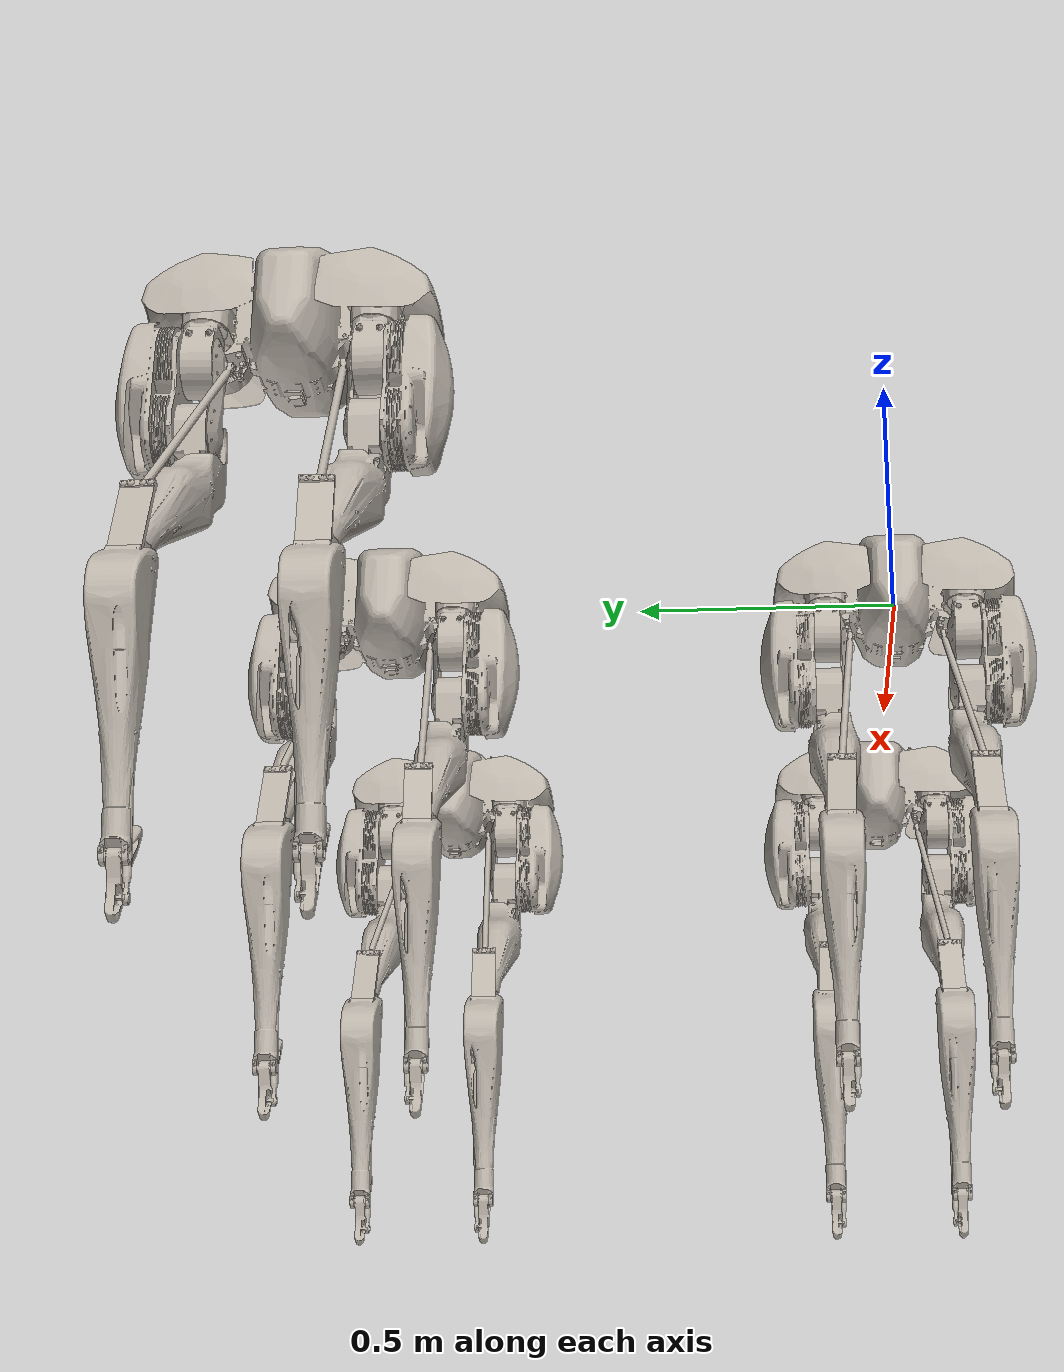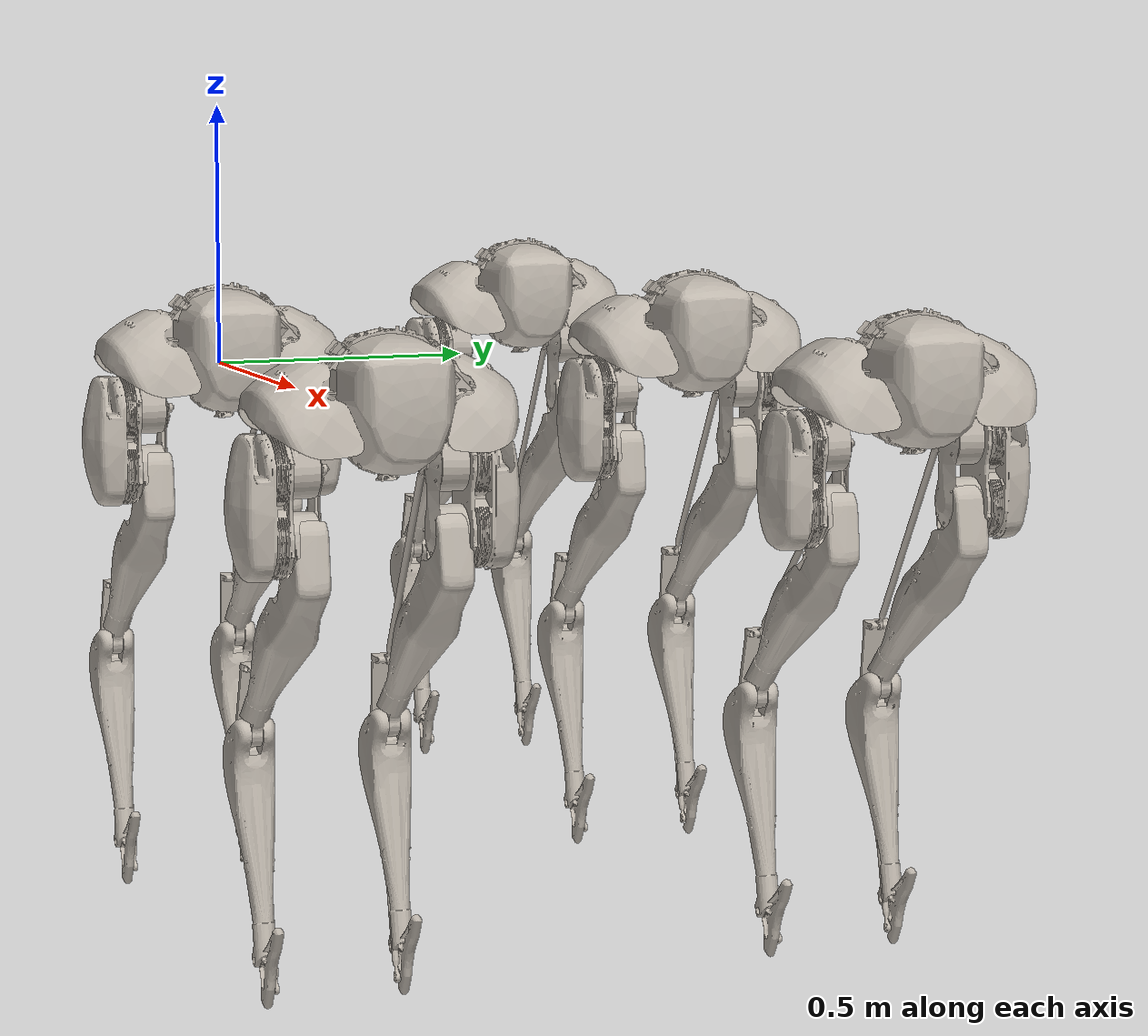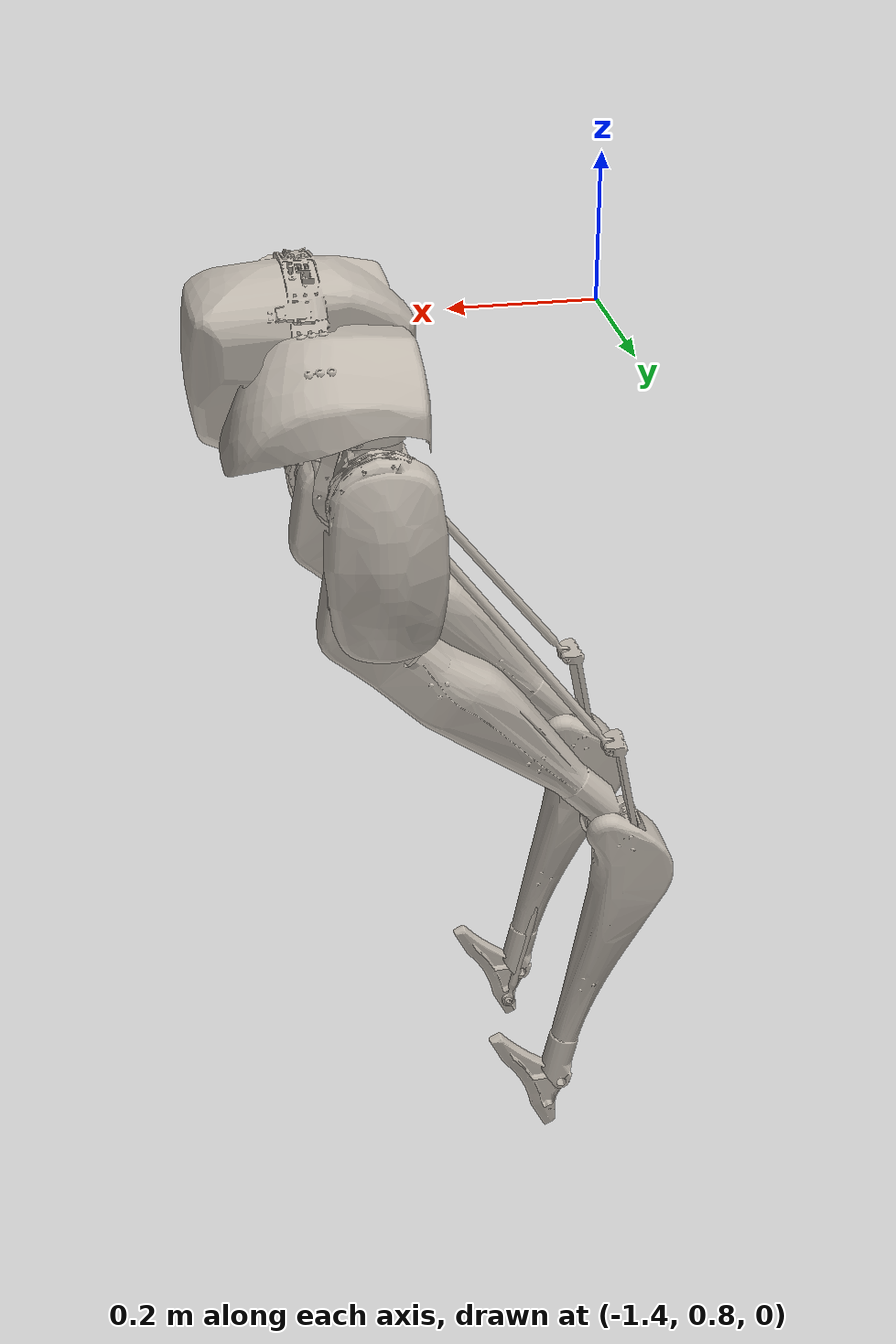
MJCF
<mujoco><compiler eulerseq="zyx" meshdir="assets" texturedir="assets" autolimits="true" />

  <option timestep="0.0005" />

  <asset>
    <texture name="cassie" file="cassie-texture.png" type="2d" />
    <material name="cassie" texture="cassie" />
    <mesh name="cassie-pelvis" file="pelvis.obj" />
    <mesh name="left-hip-roll" file="hip-roll.obj" />
    <mesh name="left-hip-yaw" file="hip-yaw.obj" />
    <mesh name="left-hip-pitch" file="hip-pitch.obj" />
    <mesh name="left-achilles-rod" file="achilles-rod.obj" />
    <mesh name="left-knee" file="knee.obj" />
    <mesh name="left-knee-spring" file="knee-spring.obj" />
    <mesh name="left-shin" file="shin.obj" />
    <mesh name="left-tarsus" file="tarsus.obj" />
    <mesh name="left-heel-spring" file="heel-spring.obj" />
    <mesh name="left-foot-crank" file="foot-crank.obj" />
    <mesh name="left-plantar-rod" file="plantar-rod.obj" />
    <mesh name="left-foot" file="foot.obj" />
    <mesh name="right-hip-roll" scale="1 -1 1" file="hip-roll.obj" />
    <mesh name="right-hip-yaw" scale="1 -1 1" file="hip-yaw.obj" />
    <mesh name="right-hip-pitch" scale="1 1 -1" file="hip-pitch.obj" />
    <mesh name="right-achilles-rod" scale="1 1 -1" file="achilles-rod.obj" />
    <mesh name="right-knee" scale="1 1 -1" file="knee.obj" />
    <mesh name="right-knee-spring" scale="1 1 -1" file="knee-spring.obj" />
    <mesh name="right-shin" scale="1 1 -1" file="shin.obj" />
    <mesh name="right-tarsus" scale="1 1 -1" file="tarsus.obj" />
    <mesh name="right-heel-spring" scale="1 1 -1" file="heel-spring.obj" />
    <mesh name="right-foot-crank" scale="1 1 -1" file="foot-crank.obj" />
    <mesh name="right-plantar-rod" scale="1 1 -1" file="plantar-rod.obj" />
    <mesh name="right-foot" scale="1 1 -1" file="foot.obj" />
  </asset>

  <worldbody><body name="cassie-pelvis_copy_0" pos="0 0 0" childclass="cassie">
      <camera name="track_copy_0" pos="0 -3 1" zaxis="0 -1 0.5" mode="track" />
      <inertial pos="0.05066 0.000346 0.02841" mass="10.33" fullinertia="0.085821 0.049222 0.08626 1.276e-05 -0.00016022 -0.000414" />
      <freejoint />
      <geom type="mesh" mesh="cassie-pelvis" euler="0 0 90" />

      <geom type="ellipsoid" size="0.15 0.12 0.13" pos="0.03 0 0.03" class="collision" />
      <geom size="0.095" fromto="-.04 0.14 .01 .02 0.14 .01" class="collision" />
      <geom size="0.095" fromto="-.04 -.14 .01 .02 -.14 .01" class="collision" />
      <site name="imu_copy_0" size="0.01" pos="0.03155 0 -0.07996" />
      <body name="left-hip-roll_copy_0" pos="0.021 0.135 0" xyaxes="0 0 -1 0 1 0">
        <inertial pos="-0.01793 0.0001 -0.04428" mass="1.82" fullinertia="0.003431 0.003793 0.002135 -6.65e-07 -0.00084 3.99e-06" />
        <joint name="left-hip-roll_copy_0" type="hinge" range="-15 22.5" damping="1" armature="0.038125" />
        <geom type="mesh" mesh="left-hip-roll" euler="0 0 90" />
        <body name="left-hip-yaw_copy_0" pos="0 0 -0.07" xyaxes="0 0 1 0 1 0">
          <inertial pos="0 -1e-05 -0.034277" mass="1.171" fullinertia="0.002443 0.002803 0.000842 -4e-08 2.462e-07 -2.71e-08" />
          <joint name="left-hip-yaw_copy_0" type="hinge" range="-22.5 22.5" damping="1" armature="0.038125" />
          <geom type="mesh" mesh="left-hip-yaw" euler="0 0 90" />
          <body name="left-hip-pitch_copy_0" pos="0 0 -0.09" xyaxes="0 0 -1 1 0 0">
            <inertial pos="0.05946 5e-05 -0.03581" mass="5.52" fullinertia="0.010898 0.029714 0.030257 -0.0002669 -5.721e-05 9.17e-06" />
            <joint name="left-hip-pitch_copy_0" type="hinge" range="-50 80" damping="1" armature="0.09344" />
            <geom type="mesh" mesh="left-hip-pitch" euler="0 0 90" />
            <geom size="0.08" fromto="0 0 -0.05 0.12 0 -0.05" class="collision" />
            <body name="left-achilles-rod_copy_0" pos="0 0 0.045" xyaxes="0.7922 -0.60599 -0.072096 0.60349 0.79547 -0.054922">
              <inertial pos="0.24719 0 0" mass="0.1567" fullinertia="3.754e-06 0.004487 0.004488 -3.74e-08 -1.61e-08 0" />
              <joint name="left-achilles-rod_copy_0" type="ball" damping="0.01" />
              <geom type="mesh" mesh="left-achilles-rod" euler="0 0 90" />
            </body>
            <body name="left-knee_copy_0" pos="0.12 0 0.0045" xyaxes="0.70711 -0.70711 0 0.70711 0.70711 0">
              <inertial pos="0.023 0.03207 -0.002181" mass="0.7578" fullinertia="0.001376 0.0010335 0.0021637 -0.00039744 -4.085e-05 -5.374e-05" />
              <joint name="left-knee_copy_0" type="hinge" ref="-45" range="-164 -37" damping="1" armature="0.09344" />
              <geom type="mesh" mesh="left-knee" euler="0 0 90" />
              <body name="left-knee-spring_copy_0" pos="0.06068 0.08241 0">
                <inertial pos="0.0836 0.0034 0" mass="0.186" fullinertia="5.215e-05 0.00041205 0.0003669 6.87e-06 0 0" />
                <geom type="mesh" mesh="left-knee-spring" euler="0 0 90" />
              </body>
              <body name="left-shin_copy_0" pos="0.06068 0.04741 0">
                <inertial pos="0.18338 0.001169 0.0002123" mass="0.577" fullinertia="0.00035939 0.014728 0.014707 -0.00020981 2.266e-05 -1.2e-07" />
                <joint name="left-shin_copy_0" type="hinge" range="-20 20" stiffness="1500" damping="0.1" />
                <geom type="mesh" mesh="left-shin" euler="0 0 90" />
                <geom size="0.04" fromto="-.06 0 0 0.17 -.01 0" class="collision-left" />
                <geom size="0.027" fromto="0.17 -.023 0 0.38 0 0" class="collision-left" />
                <geom size="0.025" fromto="-.045 .045 0 0.43476 0 0" class="collision-left" />
                <body name="left-tarsus_copy_0" pos="0.43476 0.02 0" xyaxes="0.52992 0.84805 0 -0.84805 0.52992 0">
                  <inertial pos="0.11046 -0.03058 -0.00131" mass="0.782" fullinertia="0.00039238 0.013595 0.013674 0.00023651 -4.987e-05 -4.82e-06" />
                  <joint name="left-tarsus_copy_0" type="hinge" ref="58" range="50 170" damping="0.1" />
                  <geom type="mesh" mesh="left-tarsus" euler="0 0 90" />
                  <geom size="0.028" fromto=".01 -0.03059 0.00092 0.23 -0.04 0" class="collision-left" />
                  <geom size="0.033" fromto=".04 -0.07 0.00092 0.208 -0.04 0" class="collision-left" />
                  <geom size="0.02" fromto="0.208 -0.04 0 0.43 -0.04 0" class="collision-left" />
                  <body name="left-heel-spring_copy_0" pos="-0.01269 -0.03059 0.00092" xyaxes="-0.91211 0.40829 0.036948 -0.40992 -0.90952 -0.068841">
                    <inertial pos="0.081 0.0022 0" mass="0.126" fullinertia="2.959e-05 0.00022231 0.0002007 7.15e-06 -6e-07 1e-07" />
                    <joint name="left-heel-spring_copy_0" type="hinge" stiffness="1250" />
                    <geom type="mesh" mesh="left-heel-spring" euler="0 0 90" />
                  </body>
                  <body name="left-foot-crank_copy_0" pos="0.058 -0.034 0.02275">
                    <inertial pos="0.00493 2e-05 -0.00215" mass="0.1261" fullinertia="2.6941e-05 4.9621e-05 6.3362e-05 -2.1e-09 -3.9623e-06 -1.09e-08" />
                    <joint name="left-foot-crank_copy_0" type="hinge" range="-140 -30" damping="1" />
                    <geom type="mesh" mesh="left-foot-crank" euler="0 0 90" />
                    <body name="left-plantar-rod_copy_0" pos="0.055 0 -0.00791">
                      <inertial pos="0.17792 0 0" mass="0.1186" fullinertia="2.779e-06 0.001774 0.001775 -2.34e-08 -8.1e-09 0" />
                      <joint name="left-plantar-rod_copy_0" type="hinge" />
                      <geom type="mesh" mesh="left-plantar-rod" euler="0 0 90" />
                    </body>
                  </body>
                  <body name="left-foot_copy_0" pos="0.408 -0.04 0">
                    <inertial pos="0.00474 0.02748 -0.00014" mass="0.1498" fullinertia="0.00017388 0.00016793 0.00033261 0.00011814 1.36e-06 -4e-07" />
                    <joint name="left-foot_copy_0" type="hinge" range="-140 -30" damping="1" armature="0.01225" />
                    <geom type="mesh" mesh="left-foot" euler="0 0 90" />
                    <geom size="0.02" fromto="-0.052821 0.092622 0 0.069746 -0.010224 0" class="collision-left" />
                  </body>
                </body>
              </body>
            </body>
          </body>
        </body>
      </body>
      <body name="right-hip-roll_copy_0" pos="0.021 -0.135 0" xyaxes="0 0 -1 0 1 0">
        <inertial pos="-0.01793 0.0001 -0.04428" mass="1.82" fullinertia="0.003431 0.003793 0.002135 6.65e-07 -0.00084 -3.99e-06" />
        <joint name="right-hip-roll_copy_0" type="hinge" range="-22.5 15" damping="1" armature="0.038125" />
        <geom type="mesh" mesh="right-hip-roll" euler="0 0 -90" />
        <body name="right-hip-yaw_copy_0" pos="0 0 -0.07" xyaxes="0 0 1 0 1 0">
          <inertial pos="0 1e-05 -0.034277" mass="1.171" fullinertia="0.002443 0.002803 0.000842 4e-08 2.462e-07 2.71e-08" />
          <joint name="right-hip-yaw_copy_0" type="hinge" range="-22.5 22.5" damping="1" armature="0.038125" />
          <geom type="mesh" mesh="right-hip-yaw" euler="0 0 -90" />
          <body name="right-hip-pitch_copy_0" pos="0 0 -0.09" xyaxes="0 0 -1 1 0 0">
            <inertial pos="0.05946 5e-05 0.03581" mass="5.52" fullinertia="0.010898 0.029714 0.030257 -0.0002669 5.721e-05 -9.17e-06" />
            <joint name="right-hip-pitch_copy_0" type="hinge" range="-50 80" damping="1" armature="0.09344" />
            <geom type="mesh" mesh="right-hip-pitch" euler="0 0 -90" />
            <geom size="0.08" fromto="0 0 0.05 0.12 0 0.05" class="collision" />
            <body name="right-achilles-rod_copy_0" pos="0 0 -0.045" xyaxes="0.7922 -0.60599 0.072096 0.60349 0.79547 0.054922">
              <inertial pos="0.24719 0 0" mass="0.1567" fullinertia="3.754e-06 0.004487 0.004488 -3.74e-08 1.61e-08 0" />
              <joint name="right-achilles-rod_copy_0" type="ball" damping="0.01" />
              <geom type="mesh" mesh="right-achilles-rod" euler="0 0 -90" />
            </body>
            <body name="right-knee_copy_0" pos="0.12 0 -0.0045" xyaxes="0.70711 -0.70711 0 0.70711 0.70711 0">
              <inertial pos="0.023 0.03207 0.002181" mass="0.7578" fullinertia="0.001376 0.0010335 0.0021637 -0.00039744 4.085e-05 5.374e-05" />
              <joint name="right-knee_copy_0" type="hinge" ref="-45" range="-164 -37" damping="1" armature="0.09344" />
              <geom type="mesh" mesh="right-knee" euler="0 0 -90" />
              <body name="right-knee-spring_copy_0" pos="0.06068 0.08241 0">
                <inertial pos="0.0836 0.0034 0" mass="0.186" fullinertia="5.215e-05 0.00041205 0.0003669 6.87e-06 0 0" />
                <geom type="mesh" mesh="right-knee-spring" euler="0 0 -90" />
              </body>
              <body name="right-shin_copy_0" pos="0.06068 0.04741 0">
                <inertial pos="0.18338 0.001169 -0.0002123" mass="0.577" fullinertia="0.00035939 0.014728 0.014707 -0.00020981 -2.266e-05 1.2e-07" />
                <joint name="right-shin_copy_0" type="hinge" range="-20 20" stiffness="1500" damping="0.1" />
                <geom type="mesh" mesh="right-shin" euler="0 0 -90" />
                <geom size="0.04" fromto="-.06 0 0 0.17 -.01 0" class="collision-right" />
                <geom size="0.027" fromto="0.17 -.023 0 0.38 0 0" class="collision-right" />
                <geom size="0.025" fromto="-.045 .045 0 0.43476 0 0" class="collision-right" />
                <body name="right-tarsus_copy_0" pos="0.43476 0.02 0" xyaxes="0.52992 0.84805 0 -0.84805 0.52992 0">
                  <inertial pos="0.11046 -0.03058 0.00131" mass="0.782" fullinertia="0.00039238 0.013595 0.013674 0.00023651 4.987e-05 4.82e-06" />
                  <joint name="right-tarsus_copy_0" type="hinge" ref="58" range="50 170" damping="0.1" />
                  <geom type="mesh" mesh="right-tarsus" euler="0 0 -90" />
                  <geom size="0.028" fromto=".01 -0.03059 0.00092 0.23 -0.04 0" class="collision-right" />
                  <geom size="0.033" fromto=".04 -0.07 0.00092 0.208 -0.04 0" class="collision-right" />
                  <geom size="0.02" fromto="0.208 -0.04 0 0.43 -0.04 0" class="collision-right" />
                  <body name="right-heel-spring_copy_0" pos="-0.01269 -0.03059 -0.00092" xyaxes="-0.91211 0.40829 -0.036948 -0.40992 -0.90952 0.068841">
                    <inertial pos="0.081 0.0022 0" mass="0.126" fullinertia="2.959e-05 0.00022231 0.0002007 7.15e-06 6e-07 -1e-07" />
                    <joint name="right-heel-spring_copy_0" type="hinge" stiffness="1250" />
                    <geom type="mesh" mesh="right-heel-spring" euler="0 0 -90" />
                  </body>
                  <body name="right-foot-crank_copy_0" pos="0.058 -0.034 -0.02275">
                    <inertial pos="0.00493 2e-05 0.00215" mass="0.1261" fullinertia="2.6941e-05 4.9621e-05 6.3362e-05 -2.1e-09 3.9623e-06 1.09e-08" />
                    <joint name="right-foot-crank_copy_0" type="hinge" range="-140 -30" damping="1" />
                    <geom type="mesh" mesh="right-foot-crank" euler="0 0 -90" />
                    <body name="right-plantar-rod_copy_0" pos="0.055 0 0.00791">
                      <inertial pos="0.17792 0 0" mass="0.1186" fullinertia="2.779e-06 0.001774 0.001775 -2.34e-08 8.1e-09 0" />
                      <joint name="right-plantar-rod_copy_0" type="hinge" />
                      <geom type="mesh" mesh="right-plantar-rod" euler="0 0 -90" />
                    </body>
                  </body>
                  <body name="right-foot_copy_0" pos="0.408 -0.04 0">
                    <inertial pos="0.00474 0.02748 0.00014" mass="0.1498" fullinertia="0.00017388 0.00016793 0.00033261 0.00011814 -1.36e-06 4e-07" />
                    <joint name="right-foot_copy_0" type="hinge" range="-140 -30" damping="1" armature="0.01225" />
                    <geom type="mesh" mesh="right-foot" euler="0 0 -90" />
                    <geom size="0.02" fromto="-0.052821 0.092622 0 0.069746 -0.010224 0" class="collision-right" />
                  </body>
                </body>
              </body>
            </body>
          </body>
        </body>
      </body>
    </body>
  <body name="cassie-pelvis_copy_1" pos="1 0 0" childclass="cassie">
      <camera name="track_copy_1" pos="0 -3 1" zaxis="0 -1 0.5" mode="track" />
      <inertial pos="0.05066 0.000346 0.02841" mass="10.33" fullinertia="0.085821 0.049222 0.08626 1.276e-05 -0.00016022 -0.000414" />
      <freejoint />
      <geom type="mesh" mesh="cassie-pelvis" euler="0 0 90" />

      <geom type="ellipsoid" size="0.15 0.12 0.13" pos="0.03 0 0.03" class="collision" />
      <geom size="0.095" fromto="-.04 0.14 .01 .02 0.14 .01" class="collision" />
      <geom size="0.095" fromto="-.04 -.14 .01 .02 -.14 .01" class="collision" />
      <site name="imu_copy_1" size="0.01" pos="0.03155 0 -0.07996" />
      <body name="left-hip-roll_copy_1" pos="0.021 0.135 0" xyaxes="0 0 -1 0 1 0">
        <inertial pos="-0.01793 0.0001 -0.04428" mass="1.82" fullinertia="0.003431 0.003793 0.002135 -6.65e-07 -0.00084 3.99e-06" />
        <joint name="left-hip-roll_copy_1" type="hinge" range="-15 22.5" damping="1" armature="0.038125" />
        <geom type="mesh" mesh="left-hip-roll" euler="0 0 90" />
        <body name="left-hip-yaw_copy_1" pos="0 0 -0.07" xyaxes="0 0 1 0 1 0">
          <inertial pos="0 -1e-05 -0.034277" mass="1.171" fullinertia="0.002443 0.002803 0.000842 -4e-08 2.462e-07 -2.71e-08" />
          <joint name="left-hip-yaw_copy_1" type="hinge" range="-22.5 22.5" damping="1" armature="0.038125" />
          <geom type="mesh" mesh="left-hip-yaw" euler="0 0 90" />
          <body name="left-hip-pitch_copy_1" pos="0 0 -0.09" xyaxes="0 0 -1 1 0 0">
            <inertial pos="0.05946 5e-05 -0.03581" mass="5.52" fullinertia="0.010898 0.029714 0.030257 -0.0002669 -5.721e-05 9.17e-06" />
            <joint name="left-hip-pitch_copy_1" type="hinge" range="-50 80" damping="1" armature="0.09344" />
            <geom type="mesh" mesh="left-hip-pitch" euler="0 0 90" />
            <geom size="0.08" fromto="0 0 -0.05 0.12 0 -0.05" class="collision" />
            <body name="left-achilles-rod_copy_1" pos="0 0 0.045" xyaxes="0.7922 -0.60599 -0.072096 0.60349 0.79547 -0.054922">
              <inertial pos="0.24719 0 0" mass="0.1567" fullinertia="3.754e-06 0.004487 0.004488 -3.74e-08 -1.61e-08 0" />
              <joint name="left-achilles-rod_copy_1" type="ball" damping="0.01" />
              <geom type="mesh" mesh="left-achilles-rod" euler="0 0 90" />
            </body>
            <body name="left-knee_copy_1" pos="0.12 0 0.0045" xyaxes="0.70711 -0.70711 0 0.70711 0.70711 0">
              <inertial pos="0.023 0.03207 -0.002181" mass="0.7578" fullinertia="0.001376 0.0010335 0.0021637 -0.00039744 -4.085e-05 -5.374e-05" />
              <joint name="left-knee_copy_1" type="hinge" ref="-45" range="-164 -37" damping="1" armature="0.09344" />
              <geom type="mesh" mesh="left-knee" euler="0 0 90" />
              <body name="left-knee-spring_copy_1" pos="0.06068 0.08241 0">
                <inertial pos="0.0836 0.0034 0" mass="0.186" fullinertia="5.215e-05 0.00041205 0.0003669 6.87e-06 0 0" />
                <geom type="mesh" mesh="left-knee-spring" euler="0 0 90" />
              </body>
              <body name="left-shin_copy_1" pos="0.06068 0.04741 0">
                <inertial pos="0.18338 0.001169 0.0002123" mass="0.577" fullinertia="0.00035939 0.014728 0.014707 -0.00020981 2.266e-05 -1.2e-07" />
                <joint name="left-shin_copy_1" type="hinge" range="-20 20" stiffness="1500" damping="0.1" />
                <geom type="mesh" mesh="left-shin" euler="0 0 90" />
                <geom size="0.04" fromto="-.06 0 0 0.17 -.01 0" class="collision-left" />
                <geom size="0.027" fromto="0.17 -.023 0 0.38 0 0" class="collision-left" />
                <geom size="0.025" fromto="-.045 .045 0 0.43476 0 0" class="collision-left" />
                <body name="left-tarsus_copy_1" pos="0.43476 0.02 0" xyaxes="0.52992 0.84805 0 -0.84805 0.52992 0">
                  <inertial pos="0.11046 -0.03058 -0.00131" mass="0.782" fullinertia="0.00039238 0.013595 0.013674 0.00023651 -4.987e-05 -4.82e-06" />
                  <joint name="left-tarsus_copy_1" type="hinge" ref="58" range="50 170" damping="0.1" />
                  <geom type="mesh" mesh="left-tarsus" euler="0 0 90" />
                  <geom size="0.028" fromto=".01 -0.03059 0.00092 0.23 -0.04 0" class="collision-left" />
                  <geom size="0.033" fromto=".04 -0.07 0.00092 0.208 -0.04 0" class="collision-left" />
                  <geom size="0.02" fromto="0.208 -0.04 0 0.43 -0.04 0" class="collision-left" />
                  <body name="left-heel-spring_copy_1" pos="-0.01269 -0.03059 0.00092" xyaxes="-0.91211 0.40829 0.036948 -0.40992 -0.90952 -0.068841">
                    <inertial pos="0.081 0.0022 0" mass="0.126" fullinertia="2.959e-05 0.00022231 0.0002007 7.15e-06 -6e-07 1e-07" />
                    <joint name="left-heel-spring_copy_1" type="hinge" stiffness="1250" />
                    <geom type="mesh" mesh="left-heel-spring" euler="0 0 90" />
                  </body>
                  <body name="left-foot-crank_copy_1" pos="0.058 -0.034 0.02275">
                    <inertial pos="0.00493 2e-05 -0.00215" mass="0.1261" fullinertia="2.6941e-05 4.9621e-05 6.3362e-05 -2.1e-09 -3.9623e-06 -1.09e-08" />
                    <joint name="left-foot-crank_copy_1" type="hinge" range="-140 -30" damping="1" />
                    <geom type="mesh" mesh="left-foot-crank" euler="0 0 90" />
                    <body name="left-plantar-rod_copy_1" pos="0.055 0 -0.00791">
                      <inertial pos="0.17792 0 0" mass="0.1186" fullinertia="2.779e-06 0.001774 0.001775 -2.34e-08 -8.1e-09 0" />
                      <joint name="left-plantar-rod_copy_1" type="hinge" />
                      <geom type="mesh" mesh="left-plantar-rod" euler="0 0 90" />
                    </body>
                  </body>
                  <body name="left-foot_copy_1" pos="0.408 -0.04 0">
                    <inertial pos="0.00474 0.02748 -0.00014" mass="0.1498" fullinertia="0.00017388 0.00016793 0.00033261 0.00011814 1.36e-06 -4e-07" />
                    <joint name="left-foot_copy_1" type="hinge" range="-140 -30" damping="1" armature="0.01225" />
                    <geom type="mesh" mesh="left-foot" euler="0 0 90" />
                    <geom size="0.02" fromto="-0.052821 0.092622 0 0.069746 -0.010224 0" class="collision-left" />
                  </body>
                </body>
              </body>
            </body>
          </body>
        </body>
      </body>
      <body name="right-hip-roll_copy_1" pos="0.021 -0.135 0" xyaxes="0 0 -1 0 1 0">
        <inertial pos="-0.01793 0.0001 -0.04428" mass="1.82" fullinertia="0.003431 0.003793 0.002135 6.65e-07 -0.00084 -3.99e-06" />
        <joint name="right-hip-roll_copy_1" type="hinge" range="-22.5 15" damping="1" armature="0.038125" />
        <geom type="mesh" mesh="right-hip-roll" euler="0 0 -90" />
        <body name="right-hip-yaw_copy_1" pos="0 0 -0.07" xyaxes="0 0 1 0 1 0">
          <inertial pos="0 1e-05 -0.034277" mass="1.171" fullinertia="0.002443 0.002803 0.000842 4e-08 2.462e-07 2.71e-08" />
          <joint name="right-hip-yaw_copy_1" type="hinge" range="-22.5 22.5" damping="1" armature="0.038125" />
          <geom type="mesh" mesh="right-hip-yaw" euler="0 0 -90" />
          <body name="right-hip-pitch_copy_1" pos="0 0 -0.09" xyaxes="0 0 -1 1 0 0">
            <inertial pos="0.05946 5e-05 0.03581" mass="5.52" fullinertia="0.010898 0.029714 0.030257 -0.0002669 5.721e-05 -9.17e-06" />
            <joint name="right-hip-pitch_copy_1" type="hinge" range="-50 80" damping="1" armature="0.09344" />
            <geom type="mesh" mesh="right-hip-pitch" euler="0 0 -90" />
            <geom size="0.08" fromto="0 0 0.05 0.12 0 0.05" class="collision" />
            <body name="right-achilles-rod_copy_1" pos="0 0 -0.045" xyaxes="0.7922 -0.60599 0.072096 0.60349 0.79547 0.054922">
              <inertial pos="0.24719 0 0" mass="0.1567" fullinertia="3.754e-06 0.004487 0.004488 -3.74e-08 1.61e-08 0" />
              <joint name="right-achilles-rod_copy_1" type="ball" damping="0.01" />
              <geom type="mesh" mesh="right-achilles-rod" euler="0 0 -90" />
            </body>
            <body name="right-knee_copy_1" pos="0.12 0 -0.0045" xyaxes="0.70711 -0.70711 0 0.70711 0.70711 0">
              <inertial pos="0.023 0.03207 0.002181" mass="0.7578" fullinertia="0.001376 0.0010335 0.0021637 -0.00039744 4.085e-05 5.374e-05" />
              <joint name="right-knee_copy_1" type="hinge" ref="-45" range="-164 -37" damping="1" armature="0.09344" />
              <geom type="mesh" mesh="right-knee" euler="0 0 -90" />
              <body name="right-knee-spring_copy_1" pos="0.06068 0.08241 0">
                <inertial pos="0.0836 0.0034 0" mass="0.186" fullinertia="5.215e-05 0.00041205 0.0003669 6.87e-06 0 0" />
                <geom type="mesh" mesh="right-knee-spring" euler="0 0 -90" />
              </body>
              <body name="right-shin_copy_1" pos="0.06068 0.04741 0">
                <inertial pos="0.18338 0.001169 -0.0002123" mass="0.577" fullinertia="0.00035939 0.014728 0.014707 -0.00020981 -2.266e-05 1.2e-07" />
                <joint name="right-shin_copy_1" type="hinge" range="-20 20" stiffness="1500" damping="0.1" />
                <geom type="mesh" mesh="right-shin" euler="0 0 -90" />
                <geom size="0.04" fromto="-.06 0 0 0.17 -.01 0" class="collision-right" />
                <geom size="0.027" fromto="0.17 -.023 0 0.38 0 0" class="collision-right" />
                <geom size="0.025" fromto="-.045 .045 0 0.43476 0 0" class="collision-right" />
                <body name="right-tarsus_copy_1" pos="0.43476 0.02 0" xyaxes="0.52992 0.84805 0 -0.84805 0.52992 0">
                  <inertial pos="0.11046 -0.03058 0.00131" mass="0.782" fullinertia="0.00039238 0.013595 0.013674 0.00023651 4.987e-05 4.82e-06" />
                  <joint name="right-tarsus_copy_1" type="hinge" ref="58" range="50 170" damping="0.1" />
                  <geom type="mesh" mesh="right-tarsus" euler="0 0 -90" />
                  <geom size="0.028" fromto=".01 -0.03059 0.00092 0.23 -0.04 0" class="collision-right" />
                  <geom size="0.033" fromto=".04 -0.07 0.00092 0.208 -0.04 0" class="collision-right" />
                  <geom size="0.02" fromto="0.208 -0.04 0 0.43 -0.04 0" class="collision-right" />
                  <body name="right-heel-spring_copy_1" pos="-0.01269 -0.03059 -0.00092" xyaxes="-0.91211 0.40829 -0.036948 -0.40992 -0.90952 0.068841">
                    <inertial pos="0.081 0.0022 0" mass="0.126" fullinertia="2.959e-05 0.00022231 0.0002007 7.15e-06 6e-07 -1e-07" />
                    <joint name="right-heel-spring_copy_1" type="hinge" stiffness="1250" />
                    <geom type="mesh" mesh="right-heel-spring" euler="0 0 -90" />
                  </body>
                  <body name="right-foot-crank_copy_1" pos="0.058 -0.034 -0.02275">
                    <inertial pos="0.00493 2e-05 0.00215" mass="0.1261" fullinertia="2.6941e-05 4.9621e-05 6.3362e-05 -2.1e-09 3.9623e-06 1.09e-08" />
                    <joint name="right-foot-crank_copy_1" type="hinge" range="-140 -30" damping="1" />
                    <geom type="mesh" mesh="right-foot-crank" euler="0 0 -90" />
                    <body name="right-plantar-rod_copy_1" pos="0.055 0 0.00791">
                      <inertial pos="0.17792 0 0" mass="0.1186" fullinertia="2.779e-06 0.001774 0.001775 -2.34e-08 8.1e-09 0" />
                      <joint name="right-plantar-rod_copy_1" type="hinge" />
                      <geom type="mesh" mesh="right-plantar-rod" euler="0 0 -90" />
                    </body>
                  </body>
                  <body name="right-foot_copy_1" pos="0.408 -0.04 0">
                    <inertial pos="0.00474 0.02748 0.00014" mass="0.1498" fullinertia="0.00017388 0.00016793 0.00033261 0.00011814 -1.36e-06 4e-07" />
                    <joint name="right-foot_copy_1" type="hinge" range="-140 -30" damping="1" armature="0.01225" />
                    <geom type="mesh" mesh="right-foot" euler="0 0 -90" />
                    <geom size="0.02" fromto="-0.052821 0.092622 0 0.069746 -0.010224 0" class="collision-right" />
                  </body>
                </body>
              </body>
            </body>
          </body>
        </body>
      </body>
    </body>
  <body name="cassie-pelvis_copy_2" pos="1 1 0" childclass="cassie">
      <camera name="track_copy_2" pos="0 -3 1" zaxis="0 -1 0.5" mode="track" />
      <inertial pos="0.05066 0.000346 0.02841" mass="10.33" fullinertia="0.085821 0.049222 0.08626 1.276e-05 -0.00016022 -0.000414" />
      <freejoint />
      <geom type="mesh" mesh="cassie-pelvis" euler="0 0 90" />

      <geom type="ellipsoid" size="0.15 0.12 0.13" pos="0.03 0 0.03" class="collision" />
      <geom size="0.095" fromto="-.04 0.14 .01 .02 0.14 .01" class="collision" />
      <geom size="0.095" fromto="-.04 -.14 .01 .02 -.14 .01" class="collision" />
      <site name="imu_copy_2" size="0.01" pos="0.03155 0 -0.07996" />
      <body name="left-hip-roll_copy_2" pos="0.021 0.135 0" xyaxes="0 0 -1 0 1 0">
        <inertial pos="-0.01793 0.0001 -0.04428" mass="1.82" fullinertia="0.003431 0.003793 0.002135 -6.65e-07 -0.00084 3.99e-06" />
        <joint name="left-hip-roll_copy_2" type="hinge" range="-15 22.5" damping="1" armature="0.038125" />
        <geom type="mesh" mesh="left-hip-roll" euler="0 0 90" />
        <body name="left-hip-yaw_copy_2" pos="0 0 -0.07" xyaxes="0 0 1 0 1 0">
          <inertial pos="0 -1e-05 -0.034277" mass="1.171" fullinertia="0.002443 0.002803 0.000842 -4e-08 2.462e-07 -2.71e-08" />
          <joint name="left-hip-yaw_copy_2" type="hinge" range="-22.5 22.5" damping="1" armature="0.038125" />
          <geom type="mesh" mesh="left-hip-yaw" euler="0 0 90" />
          <body name="left-hip-pitch_copy_2" pos="0 0 -0.09" xyaxes="0 0 -1 1 0 0">
            <inertial pos="0.05946 5e-05 -0.03581" mass="5.52" fullinertia="0.010898 0.029714 0.030257 -0.0002669 -5.721e-05 9.17e-06" />
            <joint name="left-hip-pitch_copy_2" type="hinge" range="-50 80" damping="1" armature="0.09344" />
            <geom type="mesh" mesh="left-hip-pitch" euler="0 0 90" />
            <geom size="0.08" fromto="0 0 -0.05 0.12 0 -0.05" class="collision" />
            <body name="left-achilles-rod_copy_2" pos="0 0 0.045" xyaxes="0.7922 -0.60599 -0.072096 0.60349 0.79547 -0.054922">
              <inertial pos="0.24719 0 0" mass="0.1567" fullinertia="3.754e-06 0.004487 0.004488 -3.74e-08 -1.61e-08 0" />
              <joint name="left-achilles-rod_copy_2" type="ball" damping="0.01" />
              <geom type="mesh" mesh="left-achilles-rod" euler="0 0 90" />
            </body>
            <body name="left-knee_copy_2" pos="0.12 0 0.0045" xyaxes="0.70711 -0.70711 0 0.70711 0.70711 0">
              <inertial pos="0.023 0.03207 -0.002181" mass="0.7578" fullinertia="0.001376 0.0010335 0.0021637 -0.00039744 -4.085e-05 -5.374e-05" />
              <joint name="left-knee_copy_2" type="hinge" ref="-45" range="-164 -37" damping="1" armature="0.09344" />
              <geom type="mesh" mesh="left-knee" euler="0 0 90" />
              <body name="left-knee-spring_copy_2" pos="0.06068 0.08241 0">
                <inertial pos="0.0836 0.0034 0" mass="0.186" fullinertia="5.215e-05 0.00041205 0.0003669 6.87e-06 0 0" />
                <geom type="mesh" mesh="left-knee-spring" euler="0 0 90" />
              </body>
              <body name="left-shin_copy_2" pos="0.06068 0.04741 0">
                <inertial pos="0.18338 0.001169 0.0002123" mass="0.577" fullinertia="0.00035939 0.014728 0.014707 -0.00020981 2.266e-05 -1.2e-07" />
                <joint name="left-shin_copy_2" type="hinge" range="-20 20" stiffness="1500" damping="0.1" />
                <geom type="mesh" mesh="left-shin" euler="0 0 90" />
                <geom size="0.04" fromto="-.06 0 0 0.17 -.01 0" class="collision-left" />
                <geom size="0.027" fromto="0.17 -.023 0 0.38 0 0" class="collision-left" />
                <geom size="0.025" fromto="-.045 .045 0 0.43476 0 0" class="collision-left" />
                <body name="left-tarsus_copy_2" pos="0.43476 0.02 0" xyaxes="0.52992 0.84805 0 -0.84805 0.52992 0">
                  <inertial pos="0.11046 -0.03058 -0.00131" mass="0.782" fullinertia="0.00039238 0.013595 0.013674 0.00023651 -4.987e-05 -4.82e-06" />
                  <joint name="left-tarsus_copy_2" type="hinge" ref="58" range="50 170" damping="0.1" />
                  <geom type="mesh" mesh="left-tarsus" euler="0 0 90" />
                  <geom size="0.028" fromto=".01 -0.03059 0.00092 0.23 -0.04 0" class="collision-left" />
                  <geom size="0.033" fromto=".04 -0.07 0.00092 0.208 -0.04 0" class="collision-left" />
                  <geom size="0.02" fromto="0.208 -0.04 0 0.43 -0.04 0" class="collision-left" />
                  <body name="left-heel-spring_copy_2" pos="-0.01269 -0.03059 0.00092" xyaxes="-0.91211 0.40829 0.036948 -0.40992 -0.90952 -0.068841">
                    <inertial pos="0.081 0.0022 0" mass="0.126" fullinertia="2.959e-05 0.00022231 0.0002007 7.15e-06 -6e-07 1e-07" />
                    <joint name="left-heel-spring_copy_2" type="hinge" stiffness="1250" />
                    <geom type="mesh" mesh="left-heel-spring" euler="0 0 90" />
                  </body>
                  <body name="left-foot-crank_copy_2" pos="0.058 -0.034 0.02275">
                    <inertial pos="0.00493 2e-05 -0.00215" mass="0.1261" fullinertia="2.6941e-05 4.9621e-05 6.3362e-05 -2.1e-09 -3.9623e-06 -1.09e-08" />
                    <joint name="left-foot-crank_copy_2" type="hinge" range="-140 -30" damping="1" />
                    <geom type="mesh" mesh="left-foot-crank" euler="0 0 90" />
                    <body name="left-plantar-rod_copy_2" pos="0.055 0 -0.00791">
                      <inertial pos="0.17792 0 0" mass="0.1186" fullinertia="2.779e-06 0.001774 0.001775 -2.34e-08 -8.1e-09 0" />
                      <joint name="left-plantar-rod_copy_2" type="hinge" />
                      <geom type="mesh" mesh="left-plantar-rod" euler="0 0 90" />
                    </body>
                  </body>
                  <body name="left-foot_copy_2" pos="0.408 -0.04 0">
                    <inertial pos="0.00474 0.02748 -0.00014" mass="0.1498" fullinertia="0.00017388 0.00016793 0.00033261 0.00011814 1.36e-06 -4e-07" />
                    <joint name="left-foot_copy_2" type="hinge" range="-140 -30" damping="1" armature="0.01225" />
                    <geom type="mesh" mesh="left-foot" euler="0 0 90" />
                    <geom size="0.02" fromto="-0.052821 0.092622 0 0.069746 -0.010224 0" class="collision-left" />
                  </body>
                </body>
              </body>
            </body>
          </body>
        </body>
      </body>
      <body name="right-hip-roll_copy_2" pos="0.021 -0.135 0" xyaxes="0 0 -1 0 1 0">
        <inertial pos="-0.01793 0.0001 -0.04428" mass="1.82" fullinertia="0.003431 0.003793 0.002135 6.65e-07 -0.00084 -3.99e-06" />
        <joint name="right-hip-roll_copy_2" type="hinge" range="-22.5 15" damping="1" armature="0.038125" />
        <geom type="mesh" mesh="right-hip-roll" euler="0 0 -90" />
        <body name="right-hip-yaw_copy_2" pos="0 0 -0.07" xyaxes="0 0 1 0 1 0">
          <inertial pos="0 1e-05 -0.034277" mass="1.171" fullinertia="0.002443 0.002803 0.000842 4e-08 2.462e-07 2.71e-08" />
          <joint name="right-hip-yaw_copy_2" type="hinge" range="-22.5 22.5" damping="1" armature="0.038125" />
          <geom type="mesh" mesh="right-hip-yaw" euler="0 0 -90" />
          <body name="right-hip-pitch_copy_2" pos="0 0 -0.09" xyaxes="0 0 -1 1 0 0">
            <inertial pos="0.05946 5e-05 0.03581" mass="5.52" fullinertia="0.010898 0.029714 0.030257 -0.0002669 5.721e-05 -9.17e-06" />
            <joint name="right-hip-pitch_copy_2" type="hinge" range="-50 80" damping="1" armature="0.09344" />
            <geom type="mesh" mesh="right-hip-pitch" euler="0 0 -90" />
            <geom size="0.08" fromto="0 0 0.05 0.12 0 0.05" class="collision" />
            <body name="right-achilles-rod_copy_2" pos="0 0 -0.045" xyaxes="0.7922 -0.60599 0.072096 0.60349 0.79547 0.054922">
              <inertial pos="0.24719 0 0" mass="0.1567" fullinertia="3.754e-06 0.004487 0.004488 -3.74e-08 1.61e-08 0" />
              <joint name="right-achilles-rod_copy_2" type="ball" damping="0.01" />
              <geom type="mesh" mesh="right-achilles-rod" euler="0 0 -90" />
            </body>
            <body name="right-knee_copy_2" pos="0.12 0 -0.0045" xyaxes="0.70711 -0.70711 0 0.70711 0.70711 0">
              <inertial pos="0.023 0.03207 0.002181" mass="0.7578" fullinertia="0.001376 0.0010335 0.0021637 -0.00039744 4.085e-05 5.374e-05" />
              <joint name="right-knee_copy_2" type="hinge" ref="-45" range="-164 -37" damping="1" armature="0.09344" />
              <geom type="mesh" mesh="right-knee" euler="0 0 -90" />
              <body name="right-knee-spring_copy_2" pos="0.06068 0.08241 0">
                <inertial pos="0.0836 0.0034 0" mass="0.186" fullinertia="5.215e-05 0.00041205 0.0003669 6.87e-06 0 0" />
                <geom type="mesh" mesh="right-knee-spring" euler="0 0 -90" />
              </body>
              <body name="right-shin_copy_2" pos="0.06068 0.04741 0">
                <inertial pos="0.18338 0.001169 -0.0002123" mass="0.577" fullinertia="0.00035939 0.014728 0.014707 -0.00020981 -2.266e-05 1.2e-07" />
                <joint name="right-shin_copy_2" type="hinge" range="-20 20" stiffness="1500" damping="0.1" />
                <geom type="mesh" mesh="right-shin" euler="0 0 -90" />
                <geom size="0.04" fromto="-.06 0 0 0.17 -.01 0" class="collision-right" />
                <geom size="0.027" fromto="0.17 -.023 0 0.38 0 0" class="collision-right" />
                <geom size="0.025" fromto="-.045 .045 0 0.43476 0 0" class="collision-right" />
                <body name="right-tarsus_copy_2" pos="0.43476 0.02 0" xyaxes="0.52992 0.84805 0 -0.84805 0.52992 0">
                  <inertial pos="0.11046 -0.03058 0.00131" mass="0.782" fullinertia="0.00039238 0.013595 0.013674 0.00023651 4.987e-05 4.82e-06" />
                  <joint name="right-tarsus_copy_2" type="hinge" ref="58" range="50 170" damping="0.1" />
                  <geom type="mesh" mesh="right-tarsus" euler="0 0 -90" />
                  <geom size="0.028" fromto=".01 -0.03059 0.00092 0.23 -0.04 0" class="collision-right" />
                  <geom size="0.033" fromto=".04 -0.07 0.00092 0.208 -0.04 0" class="collision-right" />
                  <geom size="0.02" fromto="0.208 -0.04 0 0.43 -0.04 0" class="collision-right" />
                  <body name="right-heel-spring_copy_2" pos="-0.01269 -0.03059 -0.00092" xyaxes="-0.91211 0.40829 -0.036948 -0.40992 -0.90952 0.068841">
                    <inertial pos="0.081 0.0022 0" mass="0.126" fullinertia="2.959e-05 0.00022231 0.0002007 7.15e-06 6e-07 -1e-07" />
                    <joint name="right-heel-spring_copy_2" type="hinge" stiffness="1250" />
                    <geom type="mesh" mesh="right-heel-spring" euler="0 0 -90" />
                  </body>
                  <body name="right-foot-crank_copy_2" pos="0.058 -0.034 -0.02275">
                    <inertial pos="0.00493 2e-05 0.00215" mass="0.1261" fullinertia="2.6941e-05 4.9621e-05 6.3362e-05 -2.1e-09 3.9623e-06 1.09e-08" />
                    <joint name="right-foot-crank_copy_2" type="hinge" range="-140 -30" damping="1" />
                    <geom type="mesh" mesh="right-foot-crank" euler="0 0 -90" />
                    <body name="right-plantar-rod_copy_2" pos="0.055 0 0.00791">
                      <inertial pos="0.17792 0 0" mass="0.1186" fullinertia="2.779e-06 0.001774 0.001775 -2.34e-08 8.1e-09 0" />
                      <joint name="right-plantar-rod_copy_2" type="hinge" />
                      <geom type="mesh" mesh="right-plantar-rod" euler="0 0 -90" />
                    </body>
                  </body>
                  <body name="right-foot_copy_2" pos="0.408 -0.04 0">
                    <inertial pos="0.00474 0.02748 0.00014" mass="0.1498" fullinertia="0.00017388 0.00016793 0.00033261 0.00011814 -1.36e-06 4e-07" />
                    <joint name="right-foot_copy_2" type="hinge" range="-140 -30" damping="1" armature="0.01225" />
                    <geom type="mesh" mesh="right-foot" euler="0 0 -90" />
                    <geom size="0.02" fromto="-0.052821 0.092622 0 0.069746 -0.010224 0" class="collision-right" />
                  </body>
                </body>
              </body>
            </body>
          </body>
        </body>
      </body>
    </body>
  <body name="cassie-pelvis_copy_3" pos="0 1 0" childclass="cassie">
      <camera name="track_copy_3" pos="0 -3 1" zaxis="0 -1 0.5" mode="track" />
      <inertial pos="0.05066 0.000346 0.02841" mass="10.33" fullinertia="0.085821 0.049222 0.08626 1.276e-05 -0.00016022 -0.000414" />
      <freejoint />
      <geom type="mesh" mesh="cassie-pelvis" euler="0 0 90" />

      <geom type="ellipsoid" size="0.15 0.12 0.13" pos="0.03 0 0.03" class="collision" />
      <geom size="0.095" fromto="-.04 0.14 .01 .02 0.14 .01" class="collision" />
      <geom size="0.095" fromto="-.04 -.14 .01 .02 -.14 .01" class="collision" />
      <site name="imu_copy_3" size="0.01" pos="0.03155 0 -0.07996" />
      <body name="left-hip-roll_copy_3" pos="0.021 0.135 0" xyaxes="0 0 -1 0 1 0">
        <inertial pos="-0.01793 0.0001 -0.04428" mass="1.82" fullinertia="0.003431 0.003793 0.002135 -6.65e-07 -0.00084 3.99e-06" />
        <joint name="left-hip-roll_copy_3" type="hinge" range="-15 22.5" damping="1" armature="0.038125" />
        <geom type="mesh" mesh="left-hip-roll" euler="0 0 90" />
        <body name="left-hip-yaw_copy_3" pos="0 0 -0.07" xyaxes="0 0 1 0 1 0">
          <inertial pos="0 -1e-05 -0.034277" mass="1.171" fullinertia="0.002443 0.002803 0.000842 -4e-08 2.462e-07 -2.71e-08" />
          <joint name="left-hip-yaw_copy_3" type="hinge" range="-22.5 22.5" damping="1" armature="0.038125" />
          <geom type="mesh" mesh="left-hip-yaw" euler="0 0 90" />
          <body name="left-hip-pitch_copy_3" pos="0 0 -0.09" xyaxes="0 0 -1 1 0 0">
            <inertial pos="0.05946 5e-05 -0.03581" mass="5.52" fullinertia="0.010898 0.029714 0.030257 -0.0002669 -5.721e-05 9.17e-06" />
            <joint name="left-hip-pitch_copy_3" type="hinge" range="-50 80" damping="1" armature="0.09344" />
            <geom type="mesh" mesh="left-hip-pitch" euler="0 0 90" />
            <geom size="0.08" fromto="0 0 -0.05 0.12 0 -0.05" class="collision" />
            <body name="left-achilles-rod_copy_3" pos="0 0 0.045" xyaxes="0.7922 -0.60599 -0.072096 0.60349 0.79547 -0.054922">
              <inertial pos="0.24719 0 0" mass="0.1567" fullinertia="3.754e-06 0.004487 0.004488 -3.74e-08 -1.61e-08 0" />
              <joint name="left-achilles-rod_copy_3" type="ball" damping="0.01" />
              <geom type="mesh" mesh="left-achilles-rod" euler="0 0 90" />
            </body>
            <body name="left-knee_copy_3" pos="0.12 0 0.0045" xyaxes="0.70711 -0.70711 0 0.70711 0.70711 0">
              <inertial pos="0.023 0.03207 -0.002181" mass="0.7578" fullinertia="0.001376 0.0010335 0.0021637 -0.00039744 -4.085e-05 -5.374e-05" />
              <joint name="left-knee_copy_3" type="hinge" ref="-45" range="-164 -37" damping="1" armature="0.09344" />
              <geom type="mesh" mesh="left-knee" euler="0 0 90" />
              <body name="left-knee-spring_copy_3" pos="0.06068 0.08241 0">
                <inertial pos="0.0836 0.0034 0" mass="0.186" fullinertia="5.215e-05 0.00041205 0.0003669 6.87e-06 0 0" />
                <geom type="mesh" mesh="left-knee-spring" euler="0 0 90" />
              </body>
              <body name="left-shin_copy_3" pos="0.06068 0.04741 0">
                <inertial pos="0.18338 0.001169 0.0002123" mass="0.577" fullinertia="0.00035939 0.014728 0.014707 -0.00020981 2.266e-05 -1.2e-07" />
                <joint name="left-shin_copy_3" type="hinge" range="-20 20" stiffness="1500" damping="0.1" />
                <geom type="mesh" mesh="left-shin" euler="0 0 90" />
                <geom size="0.04" fromto="-.06 0 0 0.17 -.01 0" class="collision-left" />
                <geom size="0.027" fromto="0.17 -.023 0 0.38 0 0" class="collision-left" />
                <geom size="0.025" fromto="-.045 .045 0 0.43476 0 0" class="collision-left" />
                <body name="left-tarsus_copy_3" pos="0.43476 0.02 0" xyaxes="0.52992 0.84805 0 -0.84805 0.52992 0">
                  <inertial pos="0.11046 -0.03058 -0.00131" mass="0.782" fullinertia="0.00039238 0.013595 0.013674 0.00023651 -4.987e-05 -4.82e-06" />
                  <joint name="left-tarsus_copy_3" type="hinge" ref="58" range="50 170" damping="0.1" />
                  <geom type="mesh" mesh="left-tarsus" euler="0 0 90" />
                  <geom size="0.028" fromto=".01 -0.03059 0.00092 0.23 -0.04 0" class="collision-left" />
                  <geom size="0.033" fromto=".04 -0.07 0.00092 0.208 -0.04 0" class="collision-left" />
                  <geom size="0.02" fromto="0.208 -0.04 0 0.43 -0.04 0" class="collision-left" />
                  <body name="left-heel-spring_copy_3" pos="-0.01269 -0.03059 0.00092" xyaxes="-0.91211 0.40829 0.036948 -0.40992 -0.90952 -0.068841">
                    <inertial pos="0.081 0.0022 0" mass="0.126" fullinertia="2.959e-05 0.00022231 0.0002007 7.15e-06 -6e-07 1e-07" />
                    <joint name="left-heel-spring_copy_3" type="hinge" stiffness="1250" />
                    <geom type="mesh" mesh="left-heel-spring" euler="0 0 90" />
                  </body>
                  <body name="left-foot-crank_copy_3" pos="0.058 -0.034 0.02275">
                    <inertial pos="0.00493 2e-05 -0.00215" mass="0.1261" fullinertia="2.6941e-05 4.9621e-05 6.3362e-05 -2.1e-09 -3.9623e-06 -1.09e-08" />
                    <joint name="left-foot-crank_copy_3" type="hinge" range="-140 -30" damping="1" />
                    <geom type="mesh" mesh="left-foot-crank" euler="0 0 90" />
                    <body name="left-plantar-rod_copy_3" pos="0.055 0 -0.00791">
                      <inertial pos="0.17792 0 0" mass="0.1186" fullinertia="2.779e-06 0.001774 0.001775 -2.34e-08 -8.1e-09 0" />
                      <joint name="left-plantar-rod_copy_3" type="hinge" />
                      <geom type="mesh" mesh="left-plantar-rod" euler="0 0 90" />
                    </body>
                  </body>
                  <body name="left-foot_copy_3" pos="0.408 -0.04 0">
                    <inertial pos="0.00474 0.02748 -0.00014" mass="0.1498" fullinertia="0.00017388 0.00016793 0.00033261 0.00011814 1.36e-06 -4e-07" />
                    <joint name="left-foot_copy_3" type="hinge" range="-140 -30" damping="1" armature="0.01225" />
                    <geom type="mesh" mesh="left-foot" euler="0 0 90" />
                    <geom size="0.02" fromto="-0.052821 0.092622 0 0.069746 -0.010224 0" class="collision-left" />
                  </body>
                </body>
              </body>
            </body>
          </body>
        </body>
      </body>
      <body name="right-hip-roll_copy_3" pos="0.021 -0.135 0" xyaxes="0 0 -1 0 1 0">
        <inertial pos="-0.01793 0.0001 -0.04428" mass="1.82" fullinertia="0.003431 0.003793 0.002135 6.65e-07 -0.00084 -3.99e-06" />
        <joint name="right-hip-roll_copy_3" type="hinge" range="-22.5 15" damping="1" armature="0.038125" />
        <geom type="mesh" mesh="right-hip-roll" euler="0 0 -90" />
        <body name="right-hip-yaw_copy_3" pos="0 0 -0.07" xyaxes="0 0 1 0 1 0">
          <inertial pos="0 1e-05 -0.034277" mass="1.171" fullinertia="0.002443 0.002803 0.000842 4e-08 2.462e-07 2.71e-08" />
          <joint name="right-hip-yaw_copy_3" type="hinge" range="-22.5 22.5" damping="1" armature="0.038125" />
          <geom type="mesh" mesh="right-hip-yaw" euler="0 0 -90" />
          <body name="right-hip-pitch_copy_3" pos="0 0 -0.09" xyaxes="0 0 -1 1 0 0">
            <inertial pos="0.05946 5e-05 0.03581" mass="5.52" fullinertia="0.010898 0.029714 0.030257 -0.0002669 5.721e-05 -9.17e-06" />
            <joint name="right-hip-pitch_copy_3" type="hinge" range="-50 80" damping="1" armature="0.09344" />
            <geom type="mesh" mesh="right-hip-pitch" euler="0 0 -90" />
            <geom size="0.08" fromto="0 0 0.05 0.12 0 0.05" class="collision" />
            <body name="right-achilles-rod_copy_3" pos="0 0 -0.045" xyaxes="0.7922 -0.60599 0.072096 0.60349 0.79547 0.054922">
              <inertial pos="0.24719 0 0" mass="0.1567" fullinertia="3.754e-06 0.004487 0.004488 -3.74e-08 1.61e-08 0" />
              <joint name="right-achilles-rod_copy_3" type="ball" damping="0.01" />
              <geom type="mesh" mesh="right-achilles-rod" euler="0 0 -90" />
            </body>
            <body name="right-knee_copy_3" pos="0.12 0 -0.0045" xyaxes="0.70711 -0.70711 0 0.70711 0.70711 0">
              <inertial pos="0.023 0.03207 0.002181" mass="0.7578" fullinertia="0.001376 0.0010335 0.0021637 -0.00039744 4.085e-05 5.374e-05" />
              <joint name="right-knee_copy_3" type="hinge" ref="-45" range="-164 -37" damping="1" armature="0.09344" />
              <geom type="mesh" mesh="right-knee" euler="0 0 -90" />
              <body name="right-knee-spring_copy_3" pos="0.06068 0.08241 0">
                <inertial pos="0.0836 0.0034 0" mass="0.186" fullinertia="5.215e-05 0.00041205 0.0003669 6.87e-06 0 0" />
                <geom type="mesh" mesh="right-knee-spring" euler="0 0 -90" />
              </body>
              <body name="right-shin_copy_3" pos="0.06068 0.04741 0">
                <inertial pos="0.18338 0.001169 -0.0002123" mass="0.577" fullinertia="0.00035939 0.014728 0.014707 -0.00020981 -2.266e-05 1.2e-07" />
                <joint name="right-shin_copy_3" type="hinge" range="-20 20" stiffness="1500" damping="0.1" />
                <geom type="mesh" mesh="right-shin" euler="0 0 -90" />
                <geom size="0.04" fromto="-.06 0 0 0.17 -.01 0" class="collision-right" />
                <geom size="0.027" fromto="0.17 -.023 0 0.38 0 0" class="collision-right" />
                <geom size="0.025" fromto="-.045 .045 0 0.43476 0 0" class="collision-right" />
                <body name="right-tarsus_copy_3" pos="0.43476 0.02 0" xyaxes="0.52992 0.84805 0 -0.84805 0.52992 0">
                  <inertial pos="0.11046 -0.03058 0.00131" mass="0.782" fullinertia="0.00039238 0.013595 0.013674 0.00023651 4.987e-05 4.82e-06" />
                  <joint name="right-tarsus_copy_3" type="hinge" ref="58" range="50 170" damping="0.1" />
                  <geom type="mesh" mesh="right-tarsus" euler="0 0 -90" />
                  <geom size="0.028" fromto=".01 -0.03059 0.00092 0.23 -0.04 0" class="collision-right" />
                  <geom size="0.033" fromto=".04 -0.07 0.00092 0.208 -0.04 0" class="collision-right" />
                  <geom size="0.02" fromto="0.208 -0.04 0 0.43 -0.04 0" class="collision-right" />
                  <body name="right-heel-spring_copy_3" pos="-0.01269 -0.03059 -0.00092" xyaxes="-0.91211 0.40829 -0.036948 -0.40992 -0.90952 0.068841">
                    <inertial pos="0.081 0.0022 0" mass="0.126" fullinertia="2.959e-05 0.00022231 0.0002007 7.15e-06 6e-07 -1e-07" />
                    <joint name="right-heel-spring_copy_3" type="hinge" stiffness="1250" />
                    <geom type="mesh" mesh="right-heel-spring" euler="0 0 -90" />
                  </body>
                  <body name="right-foot-crank_copy_3" pos="0.058 -0.034 -0.02275">
                    <inertial pos="0.00493 2e-05 0.00215" mass="0.1261" fullinertia="2.6941e-05 4.9621e-05 6.3362e-05 -2.1e-09 3.9623e-06 1.09e-08" />
                    <joint name="right-foot-crank_copy_3" type="hinge" range="-140 -30" damping="1" />
                    <geom type="mesh" mesh="right-foot-crank" euler="0 0 -90" />
                    <body name="right-plantar-rod_copy_3" pos="0.055 0 0.00791">
                      <inertial pos="0.17792 0 0" mass="0.1186" fullinertia="2.779e-06 0.001774 0.001775 -2.34e-08 8.1e-09 0" />
                      <joint name="right-plantar-rod_copy_3" type="hinge" />
                      <geom type="mesh" mesh="right-plantar-rod" euler="0 0 -90" />
                    </body>
                  </body>
                  <body name="right-foot_copy_3" pos="0.408 -0.04 0">
                    <inertial pos="0.00474 0.02748 0.00014" mass="0.1498" fullinertia="0.00017388 0.00016793 0.00033261 0.00011814 -1.36e-06 4e-07" />
                    <joint name="right-foot_copy_3" type="hinge" range="-140 -30" damping="1" armature="0.01225" />
                    <geom type="mesh" mesh="right-foot" euler="0 0 -90" />
                    <geom size="0.02" fromto="-0.052821 0.092622 0 0.069746 -0.010224 0" class="collision-right" />
                  </body>
                </body>
              </body>
            </body>
          </body>
        </body>
      </body>
    </body>
  <body name="cassie-pelvis_copy_4" pos="-1 1 0" childclass="cassie">
      <camera name="track_copy_4" pos="0 -3 1" zaxis="0 -1 0.5" mode="track" />
      <inertial pos="0.05066 0.000346 0.02841" mass="10.33" fullinertia="0.085821 0.049222 0.08626 1.276e-05 -0.00016022 -0.000414" />
      <freejoint />
      <geom type="mesh" mesh="cassie-pelvis" euler="0 0 90" />

      <geom type="ellipsoid" size="0.15 0.12 0.13" pos="0.03 0 0.03" class="collision" />
      <geom size="0.095" fromto="-.04 0.14 .01 .02 0.14 .01" class="collision" />
      <geom size="0.095" fromto="-.04 -.14 .01 .02 -.14 .01" class="collision" />
      <site name="imu_copy_4" size="0.01" pos="0.03155 0 -0.07996" />
      <body name="left-hip-roll_copy_4" pos="0.021 0.135 0" xyaxes="0 0 -1 0 1 0">
        <inertial pos="-0.01793 0.0001 -0.04428" mass="1.82" fullinertia="0.003431 0.003793 0.002135 -6.65e-07 -0.00084 3.99e-06" />
        <joint name="left-hip-roll_copy_4" type="hinge" range="-15 22.5" damping="1" armature="0.038125" />
        <geom type="mesh" mesh="left-hip-roll" euler="0 0 90" />
        <body name="left-hip-yaw_copy_4" pos="0 0 -0.07" xyaxes="0 0 1 0 1 0">
          <inertial pos="0 -1e-05 -0.034277" mass="1.171" fullinertia="0.002443 0.002803 0.000842 -4e-08 2.462e-07 -2.71e-08" />
          <joint name="left-hip-yaw_copy_4" type="hinge" range="-22.5 22.5" damping="1" armature="0.038125" />
          <geom type="mesh" mesh="left-hip-yaw" euler="0 0 90" />
          <body name="left-hip-pitch_copy_4" pos="0 0 -0.09" xyaxes="0 0 -1 1 0 0">
            <inertial pos="0.05946 5e-05 -0.03581" mass="5.52" fullinertia="0.010898 0.029714 0.030257 -0.0002669 -5.721e-05 9.17e-06" />
            <joint name="left-hip-pitch_copy_4" type="hinge" range="-50 80" damping="1" armature="0.09344" />
            <geom type="mesh" mesh="left-hip-pitch" euler="0 0 90" />
            <geom size="0.08" fromto="0 0 -0.05 0.12 0 -0.05" class="collision" />
            <body name="left-achilles-rod_copy_4" pos="0 0 0.045" xyaxes="0.7922 -0.60599 -0.072096 0.60349 0.79547 -0.054922">
              <inertial pos="0.24719 0 0" mass="0.1567" fullinertia="3.754e-06 0.004487 0.004488 -3.74e-08 -1.61e-08 0" />
              <joint name="left-achilles-rod_copy_4" type="ball" damping="0.01" />
              <geom type="mesh" mesh="left-achilles-rod" euler="0 0 90" />
            </body>
            <body name="left-knee_copy_4" pos="0.12 0 0.0045" xyaxes="0.70711 -0.70711 0 0.70711 0.70711 0">
              <inertial pos="0.023 0.03207 -0.002181" mass="0.7578" fullinertia="0.001376 0.0010335 0.0021637 -0.00039744 -4.085e-05 -5.374e-05" />
              <joint name="left-knee_copy_4" type="hinge" ref="-45" range="-164 -37" damping="1" armature="0.09344" />
              <geom type="mesh" mesh="left-knee" euler="0 0 90" />
              <body name="left-knee-spring_copy_4" pos="0.06068 0.08241 0">
                <inertial pos="0.0836 0.0034 0" mass="0.186" fullinertia="5.215e-05 0.00041205 0.0003669 6.87e-06 0 0" />
                <geom type="mesh" mesh="left-knee-spring" euler="0 0 90" />
              </body>
              <body name="left-shin_copy_4" pos="0.06068 0.04741 0">
                <inertial pos="0.18338 0.001169 0.0002123" mass="0.577" fullinertia="0.00035939 0.014728 0.014707 -0.00020981 2.266e-05 -1.2e-07" />
                <joint name="left-shin_copy_4" type="hinge" range="-20 20" stiffness="1500" damping="0.1" />
                <geom type="mesh" mesh="left-shin" euler="0 0 90" />
                <geom size="0.04" fromto="-.06 0 0 0.17 -.01 0" class="collision-left" />
                <geom size="0.027" fromto="0.17 -.023 0 0.38 0 0" class="collision-left" />
                <geom size="0.025" fromto="-.045 .045 0 0.43476 0 0" class="collision-left" />
                <body name="left-tarsus_copy_4" pos="0.43476 0.02 0" xyaxes="0.52992 0.84805 0 -0.84805 0.52992 0">
                  <inertial pos="0.11046 -0.03058 -0.00131" mass="0.782" fullinertia="0.00039238 0.013595 0.013674 0.00023651 -4.987e-05 -4.82e-06" />
                  <joint name="left-tarsus_copy_4" type="hinge" ref="58" range="50 170" damping="0.1" />
                  <geom type="mesh" mesh="left-tarsus" euler="0 0 90" />
                  <geom size="0.028" fromto=".01 -0.03059 0.00092 0.23 -0.04 0" class="collision-left" />
                  <geom size="0.033" fromto=".04 -0.07 0.00092 0.208 -0.04 0" class="collision-left" />
                  <geom size="0.02" fromto="0.208 -0.04 0 0.43 -0.04 0" class="collision-left" />
                  <body name="left-heel-spring_copy_4" pos="-0.01269 -0.03059 0.00092" xyaxes="-0.91211 0.40829 0.036948 -0.40992 -0.90952 -0.068841">
                    <inertial pos="0.081 0.0022 0" mass="0.126" fullinertia="2.959e-05 0.00022231 0.0002007 7.15e-06 -6e-07 1e-07" />
                    <joint name="left-heel-spring_copy_4" type="hinge" stiffness="1250" />
                    <geom type="mesh" mesh="left-heel-spring" euler="0 0 90" />
                  </body>
                  <body name="left-foot-crank_copy_4" pos="0.058 -0.034 0.02275">
                    <inertial pos="0.00493 2e-05 -0.00215" mass="0.1261" fullinertia="2.6941e-05 4.9621e-05 6.3362e-05 -2.1e-09 -3.9623e-06 -1.09e-08" />
                    <joint name="left-foot-crank_copy_4" type="hinge" range="-140 -30" damping="1" />
                    <geom type="mesh" mesh="left-foot-crank" euler="0 0 90" />
                    <body name="left-plantar-rod_copy_4" pos="0.055 0 -0.00791">
                      <inertial pos="0.17792 0 0" mass="0.1186" fullinertia="2.779e-06 0.001774 0.001775 -2.34e-08 -8.1e-09 0" />
                      <joint name="left-plantar-rod_copy_4" type="hinge" />
                      <geom type="mesh" mesh="left-plantar-rod" euler="0 0 90" />
                    </body>
                  </body>
                  <body name="left-foot_copy_4" pos="0.408 -0.04 0">
                    <inertial pos="0.00474 0.02748 -0.00014" mass="0.1498" fullinertia="0.00017388 0.00016793 0.00033261 0.00011814 1.36e-06 -4e-07" />
                    <joint name="left-foot_copy_4" type="hinge" range="-140 -30" damping="1" armature="0.01225" />
                    <geom type="mesh" mesh="left-foot" euler="0 0 90" />
                    <geom size="0.02" fromto="-0.052821 0.092622 0 0.069746 -0.010224 0" class="collision-left" />
                  </body>
                </body>
              </body>
            </body>
          </body>
        </body>
      </body>
      <body name="right-hip-roll_copy_4" pos="0.021 -0.135 0" xyaxes="0 0 -1 0 1 0">
        <inertial pos="-0.01793 0.0001 -0.04428" mass="1.82" fullinertia="0.003431 0.003793 0.002135 6.65e-07 -0.00084 -3.99e-06" />
        <joint name="right-hip-roll_copy_4" type="hinge" range="-22.5 15" damping="1" armature="0.038125" />
        <geom type="mesh" mesh="right-hip-roll" euler="0 0 -90" />
        <body name="right-hip-yaw_copy_4" pos="0 0 -0.07" xyaxes="0 0 1 0 1 0">
          <inertial pos="0 1e-05 -0.034277" mass="1.171" fullinertia="0.002443 0.002803 0.000842 4e-08 2.462e-07 2.71e-08" />
          <joint name="right-hip-yaw_copy_4" type="hinge" range="-22.5 22.5" damping="1" armature="0.038125" />
          <geom type="mesh" mesh="right-hip-yaw" euler="0 0 -90" />
          <body name="right-hip-pitch_copy_4" pos="0 0 -0.09" xyaxes="0 0 -1 1 0 0">
            <inertial pos="0.05946 5e-05 0.03581" mass="5.52" fullinertia="0.010898 0.029714 0.030257 -0.0002669 5.721e-05 -9.17e-06" />
            <joint name="right-hip-pitch_copy_4" type="hinge" range="-50 80" damping="1" armature="0.09344" />
            <geom type="mesh" mesh="right-hip-pitch" euler="0 0 -90" />
            <geom size="0.08" fromto="0 0 0.05 0.12 0 0.05" class="collision" />
            <body name="right-achilles-rod_copy_4" pos="0 0 -0.045" xyaxes="0.7922 -0.60599 0.072096 0.60349 0.79547 0.054922">
              <inertial pos="0.24719 0 0" mass="0.1567" fullinertia="3.754e-06 0.004487 0.004488 -3.74e-08 1.61e-08 0" />
              <joint name="right-achilles-rod_copy_4" type="ball" damping="0.01" />
              <geom type="mesh" mesh="right-achilles-rod" euler="0 0 -90" />
            </body>
            <body name="right-knee_copy_4" pos="0.12 0 -0.0045" xyaxes="0.70711 -0.70711 0 0.70711 0.70711 0">
              <inertial pos="0.023 0.03207 0.002181" mass="0.7578" fullinertia="0.001376 0.0010335 0.0021637 -0.00039744 4.085e-05 5.374e-05" />
              <joint name="right-knee_copy_4" type="hinge" ref="-45" range="-164 -37" damping="1" armature="0.09344" />
              <geom type="mesh" mesh="right-knee" euler="0 0 -90" />
              <body name="right-knee-spring_copy_4" pos="0.06068 0.08241 0">
                <inertial pos="0.0836 0.0034 0" mass="0.186" fullinertia="5.215e-05 0.00041205 0.0003669 6.87e-06 0 0" />
                <geom type="mesh" mesh="right-knee-spring" euler="0 0 -90" />
              </body>
              <body name="right-shin_copy_4" pos="0.06068 0.04741 0">
                <inertial pos="0.18338 0.001169 -0.0002123" mass="0.577" fullinertia="0.00035939 0.014728 0.014707 -0.00020981 -2.266e-05 1.2e-07" />
                <joint name="right-shin_copy_4" type="hinge" range="-20 20" stiffness="1500" damping="0.1" />
                <geom type="mesh" mesh="right-shin" euler="0 0 -90" />
                <geom size="0.04" fromto="-.06 0 0 0.17 -.01 0" class="collision-right" />
                <geom size="0.027" fromto="0.17 -.023 0 0.38 0 0" class="collision-right" />
                <geom size="0.025" fromto="-.045 .045 0 0.43476 0 0" class="collision-right" />
                <body name="right-tarsus_copy_4" pos="0.43476 0.02 0" xyaxes="0.52992 0.84805 0 -0.84805 0.52992 0">
                  <inertial pos="0.11046 -0.03058 0.00131" mass="0.782" fullinertia="0.00039238 0.013595 0.013674 0.00023651 4.987e-05 4.82e-06" />
                  <joint name="right-tarsus_copy_4" type="hinge" ref="58" range="50 170" damping="0.1" />
                  <geom type="mesh" mesh="right-tarsus" euler="0 0 -90" />
                  <geom size="0.028" fromto=".01 -0.03059 0.00092 0.23 -0.04 0" class="collision-right" />
                  <geom size="0.033" fromto=".04 -0.07 0.00092 0.208 -0.04 0" class="collision-right" />
                  <geom size="0.02" fromto="0.208 -0.04 0 0.43 -0.04 0" class="collision-right" />
                  <body name="right-heel-spring_copy_4" pos="-0.01269 -0.03059 -0.00092" xyaxes="-0.91211 0.40829 -0.036948 -0.40992 -0.90952 0.068841">
                    <inertial pos="0.081 0.0022 0" mass="0.126" fullinertia="2.959e-05 0.00022231 0.0002007 7.15e-06 6e-07 -1e-07" />
                    <joint name="right-heel-spring_copy_4" type="hinge" stiffness="1250" />
                    <geom type="mesh" mesh="right-heel-spring" euler="0 0 -90" />
                  </body>
                  <body name="right-foot-crank_copy_4" pos="0.058 -0.034 -0.02275">
                    <inertial pos="0.00493 2e-05 0.00215" mass="0.1261" fullinertia="2.6941e-05 4.9621e-05 6.3362e-05 -2.1e-09 3.9623e-06 1.09e-08" />
                    <joint name="right-foot-crank_copy_4" type="hinge" range="-140 -30" damping="1" />
                    <geom type="mesh" mesh="right-foot-crank" euler="0 0 -90" />
                    <body name="right-plantar-rod_copy_4" pos="0.055 0 0.00791">
                      <inertial pos="0.17792 0 0" mass="0.1186" fullinertia="2.779e-06 0.001774 0.001775 -2.34e-08 8.1e-09 0" />
                      <joint name="right-plantar-rod_copy_4" type="hinge" />
                      <geom type="mesh" mesh="right-plantar-rod" euler="0 0 -90" />
                    </body>
                  </body>
                  <body name="right-foot_copy_4" pos="0.408 -0.04 0">
                    <inertial pos="0.00474 0.02748 0.00014" mass="0.1498" fullinertia="0.00017388 0.00016793 0.00033261 0.00011814 -1.36e-06 4e-07" />
                    <joint name="right-foot_copy_4" type="hinge" range="-140 -30" damping="1" armature="0.01225" />
                    <geom type="mesh" mesh="right-foot" euler="0 0 -90" />
                    <geom size="0.02" fromto="-0.052821 0.092622 0 0.069746 -0.010224 0" class="collision-right" />
                  </body>
                </body>
              </body>
            </body>
          </body>
        </body>
      </body>
    </body>
  </worldbody><actuator><motor name="left-hip-roll_copy_0" joint="left-hip-roll_copy_0" gear="25" ctrlrange="-4.5 4.5" user="2900" />
    <motor name="left-hip-yaw_copy_0" joint="left-hip-yaw_copy_0" gear="25" ctrlrange="-4.5 4.5" user="2900" />
    <motor name="left-hip-pitch_copy_0" joint="left-hip-pitch_copy_0" gear="16" ctrlrange="-12.2 12.2" user="1300" />
    <motor name="left-knee_copy_0" joint="left-knee_copy_0" gear="16" ctrlrange="-12.2 12.2" user="1300" />
    <motor name="left-foot_copy_0" joint="left-foot_copy_0" gear="50" ctrlrange="-0.9 0.9" user="5500" />
    <motor name="right-hip-roll_copy_0" joint="right-hip-roll_copy_0" gear="25" ctrlrange="-4.5 4.5" user="2900" />
    <motor name="right-hip-yaw_copy_0" joint="right-hip-yaw_copy_0" gear="25" ctrlrange="-4.5 4.5" user="2900" />
    <motor name="right-hip-pitch_copy_0" joint="right-hip-pitch_copy_0" gear="16" ctrlrange="-12.2 12.2" user="1300" />
    <motor name="right-knee_copy_0" joint="right-knee_copy_0" gear="16" ctrlrange="-12.2 12.2" user="1300" />
    <motor name="right-foot_copy_0" joint="right-foot_copy_0" gear="50" ctrlrange="-0.9 0.9" user="5500" />
  <motor name="left-hip-roll_copy_1" joint="left-hip-roll_copy_1" gear="25" ctrlrange="-4.5 4.5" user="2900" />
    <motor name="left-hip-yaw_copy_1" joint="left-hip-yaw_copy_1" gear="25" ctrlrange="-4.5 4.5" user="2900" />
    <motor name="left-hip-pitch_copy_1" joint="left-hip-pitch_copy_1" gear="16" ctrlrange="-12.2 12.2" user="1300" />
    <motor name="left-knee_copy_1" joint="left-knee_copy_1" gear="16" ctrlrange="-12.2 12.2" user="1300" />
    <motor name="left-foot_copy_1" joint="left-foot_copy_1" gear="50" ctrlrange="-0.9 0.9" user="5500" />
    <motor name="right-hip-roll_copy_1" joint="right-hip-roll_copy_1" gear="25" ctrlrange="-4.5 4.5" user="2900" />
    <motor name="right-hip-yaw_copy_1" joint="right-hip-yaw_copy_1" gear="25" ctrlrange="-4.5 4.5" user="2900" />
    <motor name="right-hip-pitch_copy_1" joint="right-hip-pitch_copy_1" gear="16" ctrlrange="-12.2 12.2" user="1300" />
    <motor name="right-knee_copy_1" joint="right-knee_copy_1" gear="16" ctrlrange="-12.2 12.2" user="1300" />
    <motor name="right-foot_copy_1" joint="right-foot_copy_1" gear="50" ctrlrange="-0.9 0.9" user="5500" />
  <motor name="left-hip-roll_copy_2" joint="left-hip-roll_copy_2" gear="25" ctrlrange="-4.5 4.5" user="2900" />
    <motor name="left-hip-yaw_copy_2" joint="left-hip-yaw_copy_2" gear="25" ctrlrange="-4.5 4.5" user="2900" />
    <motor name="left-hip-pitch_copy_2" joint="left-hip-pitch_copy_2" gear="16" ctrlrange="-12.2 12.2" user="1300" />
    <motor name="left-knee_copy_2" joint="left-knee_copy_2" gear="16" ctrlrange="-12.2 12.2" user="1300" />
    <motor name="left-foot_copy_2" joint="left-foot_copy_2" gear="50" ctrlrange="-0.9 0.9" user="5500" />
    <motor name="right-hip-roll_copy_2" joint="right-hip-roll_copy_2" gear="25" ctrlrange="-4.5 4.5" user="2900" />
    <motor name="right-hip-yaw_copy_2" joint="right-hip-yaw_copy_2" gear="25" ctrlrange="-4.5 4.5" user="2900" />
    <motor name="right-hip-pitch_copy_2" joint="right-hip-pitch_copy_2" gear="16" ctrlrange="-12.2 12.2" user="1300" />
    <motor name="right-knee_copy_2" joint="right-knee_copy_2" gear="16" ctrlrange="-12.2 12.2" user="1300" />
    <motor name="right-foot_copy_2" joint="right-foot_copy_2" gear="50" ctrlrange="-0.9 0.9" user="5500" />
  <motor name="left-hip-roll_copy_3" joint="left-hip-roll_copy_3" gear="25" ctrlrange="-4.5 4.5" user="2900" />
    <motor name="left-hip-yaw_copy_3" joint="left-hip-yaw_copy_3" gear="25" ctrlrange="-4.5 4.5" user="2900" />
    <motor name="left-hip-pitch_copy_3" joint="left-hip-pitch_copy_3" gear="16" ctrlrange="-12.2 12.2" user="1300" />
    <motor name="left-knee_copy_3" joint="left-knee_copy_3" gear="16" ctrlrange="-12.2 12.2" user="1300" />
    <motor name="left-foot_copy_3" joint="left-foot_copy_3" gear="50" ctrlrange="-0.9 0.9" user="5500" />
    <motor name="right-hip-roll_copy_3" joint="right-hip-roll_copy_3" gear="25" ctrlrange="-4.5 4.5" user="2900" />
    <motor name="right-hip-yaw_copy_3" joint="right-hip-yaw_copy_3" gear="25" ctrlrange="-4.5 4.5" user="2900" />
    <motor name="right-hip-pitch_copy_3" joint="right-hip-pitch_copy_3" gear="16" ctrlrange="-12.2 12.2" user="1300" />
    <motor name="right-knee_copy_3" joint="right-knee_copy_3" gear="16" ctrlrange="-12.2 12.2" user="1300" />
    <motor name="right-foot_copy_3" joint="right-foot_copy_3" gear="50" ctrlrange="-0.9 0.9" user="5500" />
  <motor name="left-hip-roll_copy_4" joint="left-hip-roll_copy_4" gear="25" ctrlrange="-4.5 4.5" user="2900" />
    <motor name="left-hip-yaw_copy_4" joint="left-hip-yaw_copy_4" gear="25" ctrlrange="-4.5 4.5" user="2900" />
    <motor name="left-hip-pitch_copy_4" joint="left-hip-pitch_copy_4" gear="16" ctrlrange="-12.2 12.2" user="1300" />
    <motor name="left-knee_copy_4" joint="left-knee_copy_4" gear="16" ctrlrange="-12.2 12.2" user="1300" />
    <motor name="left-foot_copy_4" joint="left-foot_copy_4" gear="50" ctrlrange="-0.9 0.9" user="5500" />
    <motor name="right-hip-roll_copy_4" joint="right-hip-roll_copy_4" gear="25" ctrlrange="-4.5 4.5" user="2900" />
    <motor name="right-hip-yaw_copy_4" joint="right-hip-yaw_copy_4" gear="25" ctrlrange="-4.5 4.5" user="2900" />
    <motor name="right-hip-pitch_copy_4" joint="right-hip-pitch_copy_4" gear="16" ctrlrange="-12.2 12.2" user="1300" />
    <motor name="right-knee_copy_4" joint="right-knee_copy_4" gear="16" ctrlrange="-12.2 12.2" user="1300" />
    <motor name="right-foot_copy_4" joint="right-foot_copy_4" gear="50" ctrlrange="-0.9 0.9" user="5500" />
  </actuator><sensor><actuatorpos name="left-hip-roll-input_copy_0" actuator="left-hip-roll_copy_0" user="13" />
    <actuatorpos name="left-hip-yaw-input_copy_0" actuator="left-hip-yaw_copy_0" user="13" />
    <actuatorpos name="left-hip-pitch-input_copy_0" actuator="left-hip-pitch_copy_0" user="13" />
    <actuatorpos name="left-knee-input_copy_0" actuator="left-knee_copy_0" user="13" />
    <actuatorpos name="left-foot-input_copy_0" actuator="left-foot_copy_0" user="18" />

    <jointpos name="left-shin-output_copy_0" joint="left-shin_copy_0" user="18" noise="2e-4" />
    <jointpos name="left-tarsus-output_copy_0" joint="left-tarsus_copy_0" user="18" noise="2e-4" />
    <jointpos name="left-foot-output_copy_0" joint="left-foot_copy_0" user="13" />

    <actuatorpos name="right-hip-roll-input_copy_0" actuator="right-hip-roll_copy_0" user="13" />
    <actuatorpos name="right-hip-yaw-input_copy_0" actuator="right-hip-yaw_copy_0" user="13" />
    <actuatorpos name="right-hip-pitch-input_copy_0" actuator="right-hip-pitch_copy_0" user="13" />
    <actuatorpos name="right-knee-input_copy_0" actuator="right-knee_copy_0" user="13" />
    <actuatorpos name="right-foot-input_copy_0" actuator="right-foot_copy_0" user="18" />

    <jointpos name="right-shin-output_copy_0" joint="right-shin_copy_0" user="18" noise="2e-4" />
    <jointpos name="right-tarsus-output_copy_0" joint="right-tarsus_copy_0" user="18" noise="2e-4" />
    <jointpos name="right-foot-output_copy_0" joint="right-foot_copy_0" user="13" />

    <framequat name="pelvis-orientation_copy_0" objtype="site" objname="imu_copy_0" />
    <gyro name="pelvis-angular-velocity_copy_0" site="imu_copy_0" noise="5e-4" cutoff="34.9" />
    <accelerometer name="pelvis-linear-acceleration_copy_0" site="imu_copy_0" noise="1e-2" cutoff="157" />
    <magnetometer name="pelvis-magnetometer_copy_0" site="imu_copy_0" />
  <actuatorpos name="left-hip-roll-input_copy_1" actuator="left-hip-roll_copy_1" user="13" />
    <actuatorpos name="left-hip-yaw-input_copy_1" actuator="left-hip-yaw_copy_1" user="13" />
    <actuatorpos name="left-hip-pitch-input_copy_1" actuator="left-hip-pitch_copy_1" user="13" />
    <actuatorpos name="left-knee-input_copy_1" actuator="left-knee_copy_1" user="13" />
    <actuatorpos name="left-foot-input_copy_1" actuator="left-foot_copy_1" user="18" />

    <jointpos name="left-shin-output_copy_1" joint="left-shin_copy_1" user="18" noise="2e-4" />
    <jointpos name="left-tarsus-output_copy_1" joint="left-tarsus_copy_1" user="18" noise="2e-4" />
    <jointpos name="left-foot-output_copy_1" joint="left-foot_copy_1" user="13" />

    <actuatorpos name="right-hip-roll-input_copy_1" actuator="right-hip-roll_copy_1" user="13" />
    <actuatorpos name="right-hip-yaw-input_copy_1" actuator="right-hip-yaw_copy_1" user="13" />
    <actuatorpos name="right-hip-pitch-input_copy_1" actuator="right-hip-pitch_copy_1" user="13" />
    <actuatorpos name="right-knee-input_copy_1" actuator="right-knee_copy_1" user="13" />
    <actuatorpos name="right-foot-input_copy_1" actuator="right-foot_copy_1" user="18" />

    <jointpos name="right-shin-output_copy_1" joint="right-shin_copy_1" user="18" noise="2e-4" />
    <jointpos name="right-tarsus-output_copy_1" joint="right-tarsus_copy_1" user="18" noise="2e-4" />
    <jointpos name="right-foot-output_copy_1" joint="right-foot_copy_1" user="13" />

    <framequat name="pelvis-orientation_copy_1" objtype="site" objname="imu_copy_1" />
    <gyro name="pelvis-angular-velocity_copy_1" site="imu_copy_1" noise="5e-4" cutoff="34.9" />
    <accelerometer name="pelvis-linear-acceleration_copy_1" site="imu_copy_1" noise="1e-2" cutoff="157" />
    <magnetometer name="pelvis-magnetometer_copy_1" site="imu_copy_1" />
  <actuatorpos name="left-hip-roll-input_copy_2" actuator="left-hip-roll_copy_2" user="13" />
    <actuatorpos name="left-hip-yaw-input_copy_2" actuator="left-hip-yaw_copy_2" user="13" />
    <actuatorpos name="left-hip-pitch-input_copy_2" actuator="left-hip-pitch_copy_2" user="13" />
    <actuatorpos name="left-knee-input_copy_2" actuator="left-knee_copy_2" user="13" />
    <actuatorpos name="left-foot-input_copy_2" actuator="left-foot_copy_2" user="18" />

    <jointpos name="left-shin-output_copy_2" joint="left-shin_copy_2" user="18" noise="2e-4" />
    <jointpos name="left-tarsus-output_copy_2" joint="left-tarsus_copy_2" user="18" noise="2e-4" />
    <jointpos name="left-foot-output_copy_2" joint="left-foot_copy_2" user="13" />

    <actuatorpos name="right-hip-roll-input_copy_2" actuator="right-hip-roll_copy_2" user="13" />
    <actuatorpos name="right-hip-yaw-input_copy_2" actuator="right-hip-yaw_copy_2" user="13" />
    <actuatorpos name="right-hip-pitch-input_copy_2" actuator="right-hip-pitch_copy_2" user="13" />
    <actuatorpos name="right-knee-input_copy_2" actuator="right-knee_copy_2" user="13" />
    <actuatorpos name="right-foot-input_copy_2" actuator="right-foot_copy_2" user="18" />

    <jointpos name="right-shin-output_copy_2" joint="right-shin_copy_2" user="18" noise="2e-4" />
    <jointpos name="right-tarsus-output_copy_2" joint="right-tarsus_copy_2" user="18" noise="2e-4" />
    <jointpos name="right-foot-output_copy_2" joint="right-foot_copy_2" user="13" />

    <framequat name="pelvis-orientation_copy_2" objtype="site" objname="imu_copy_2" />
    <gyro name="pelvis-angular-velocity_copy_2" site="imu_copy_2" noise="5e-4" cutoff="34.9" />
    <accelerometer name="pelvis-linear-acceleration_copy_2" site="imu_copy_2" noise="1e-2" cutoff="157" />
    <magnetometer name="pelvis-magnetometer_copy_2" site="imu_copy_2" />
  <actuatorpos name="left-hip-roll-input_copy_3" actuator="left-hip-roll_copy_3" user="13" />
    <actuatorpos name="left-hip-yaw-input_copy_3" actuator="left-hip-yaw_copy_3" user="13" />
    <actuatorpos name="left-hip-pitch-input_copy_3" actuator="left-hip-pitch_copy_3" user="13" />
    <actuatorpos name="left-knee-input_copy_3" actuator="left-knee_copy_3" user="13" />
    <actuatorpos name="left-foot-input_copy_3" actuator="left-foot_copy_3" user="18" />

    <jointpos name="left-shin-output_copy_3" joint="left-shin_copy_3" user="18" noise="2e-4" />
    <jointpos name="left-tarsus-output_copy_3" joint="left-tarsus_copy_3" user="18" noise="2e-4" />
    <jointpos name="left-foot-output_copy_3" joint="left-foot_copy_3" user="13" />

    <actuatorpos name="right-hip-roll-input_copy_3" actuator="right-hip-roll_copy_3" user="13" />
    <actuatorpos name="right-hip-yaw-input_copy_3" actuator="right-hip-yaw_copy_3" user="13" />
    <actuatorpos name="right-hip-pitch-input_copy_3" actuator="right-hip-pitch_copy_3" user="13" />
    <actuatorpos name="right-knee-input_copy_3" actuator="right-knee_copy_3" user="13" />
    <actuatorpos name="right-foot-input_copy_3" actuator="right-foot_copy_3" user="18" />

    <jointpos name="right-shin-output_copy_3" joint="right-shin_copy_3" user="18" noise="2e-4" />
    <jointpos name="right-tarsus-output_copy_3" joint="right-tarsus_copy_3" user="18" noise="2e-4" />
    <jointpos name="right-foot-output_copy_3" joint="right-foot_copy_3" user="13" />

    <framequat name="pelvis-orientation_copy_3" objtype="site" objname="imu_copy_3" />
    <gyro name="pelvis-angular-velocity_copy_3" site="imu_copy_3" noise="5e-4" cutoff="34.9" />
    <accelerometer name="pelvis-linear-acceleration_copy_3" site="imu_copy_3" noise="1e-2" cutoff="157" />
    <magnetometer name="pelvis-magnetometer_copy_3" site="imu_copy_3" />
  <actuatorpos name="left-hip-roll-input_copy_4" actuator="left-hip-roll_copy_4" user="13" />
    <actuatorpos name="left-hip-yaw-input_copy_4" actuator="left-hip-yaw_copy_4" user="13" />
    <actuatorpos name="left-hip-pitch-input_copy_4" actuator="left-hip-pitch_copy_4" user="13" />
    <actuatorpos name="left-knee-input_copy_4" actuator="left-knee_copy_4" user="13" />
    <actuatorpos name="left-foot-input_copy_4" actuator="left-foot_copy_4" user="18" />

    <jointpos name="left-shin-output_copy_4" joint="left-shin_copy_4" user="18" noise="2e-4" />
    <jointpos name="left-tarsus-output_copy_4" joint="left-tarsus_copy_4" user="18" noise="2e-4" />
    <jointpos name="left-foot-output_copy_4" joint="left-foot_copy_4" user="13" />

    <actuatorpos name="right-hip-roll-input_copy_4" actuator="right-hip-roll_copy_4" user="13" />
    <actuatorpos name="right-hip-yaw-input_copy_4" actuator="right-hip-yaw_copy_4" user="13" />
    <actuatorpos name="right-hip-pitch-input_copy_4" actuator="right-hip-pitch_copy_4" user="13" />
    <actuatorpos name="right-knee-input_copy_4" actuator="right-knee_copy_4" user="13" />
    <actuatorpos name="right-foot-input_copy_4" actuator="right-foot_copy_4" user="18" />

    <jointpos name="right-shin-output_copy_4" joint="right-shin_copy_4" user="18" noise="2e-4" />
    <jointpos name="right-tarsus-output_copy_4" joint="right-tarsus_copy_4" user="18" noise="2e-4" />
    <jointpos name="right-foot-output_copy_4" joint="right-foot_copy_4" user="13" />

    <framequat name="pelvis-orientation_copy_4" objtype="site" objname="imu_copy_4" />
    <gyro name="pelvis-angular-velocity_copy_4" site="imu_copy_4" noise="5e-4" cutoff="34.9" />
    <accelerometer name="pelvis-linear-acceleration_copy_4" site="imu_copy_4" noise="1e-2" cutoff="157" />
    <magnetometer name="pelvis-magnetometer_copy_4" site="imu_copy_4" />
  </sensor><keyframe>
    <key name="home" qpos="0 0 1.0059301 1 0 0 0 0.00449956 0 0.497301 0.97861 -0.0164104 0.0177766         -0.204298 -1.1997 0 1.42671 -2.25907e-06 -1.52439 1.50645 -1.59681 -0.00449956 0 0.497301         0.97874 0.0038687 -0.0151572 -0.204509 -1.1997 0 1.42671 0 -1.52439 1.50645 -1.59681 0 0 1.0059301 1 0 0 0 0.00449956 0 0.497301 0.97861 -0.0164104 0.0177766         -0.204298 -1.1997 0 1.42671 -2.25907e-06 -1.52439 1.50645 -1.59681 -0.00449956 0 0.497301         0.97874 0.0038687 -0.0151572 -0.204509 -1.1997 0 1.42671 0 -1.52439 1.50645 -1.59681 0 0 1.0059301 1 0 0 0 0.00449956 0 0.497301 0.97861 -0.0164104 0.0177766         -0.204298 -1.1997 0 1.42671 -2.25907e-06 -1.52439 1.50645 -1.59681 -0.00449956 0 0.497301         0.97874 0.0038687 -0.0151572 -0.204509 -1.1997 0 1.42671 0 -1.52439 1.50645 -1.59681 0 0 1.0059301 1 0 0 0 0.00449956 0 0.497301 0.97861 -0.0164104 0.0177766         -0.204298 -1.1997 0 1.42671 -2.25907e-06 -1.52439 1.50645 -1.59681 -0.00449956 0 0.497301         0.97874 0.0038687 -0.0151572 -0.204509 -1.1997 0 1.42671 0 -1.52439 1.50645 -1.59681 0 0 1.0059301 1 0 0 0 0.00449956 0 0.497301 0.97861 -0.0164104 0.0177766         -0.204298 -1.1997 0 1.42671 -2.25907e-06 -1.52439 1.50645 -1.59681 -0.00449956 0 0.497301         0.97874 0.0038687 -0.0151572 -0.204509 -1.1997 0 1.42671 0 -1.52439 1.50645 -1.59681" />
  </keyframe>
<equality /><default>
    <geom contype="0" conaffinity="0" condim="1" solref="0.005 1" />
    <equality solref="0.005 1" />
    <default class="cassie">
      <geom material="cassie" group="2" />
    </default>
    <default class="collision">
      <geom contype="1" group="3" type="capsule" />
      <default class="collision-left">
        <geom contype="2" conaffinity="4" />
      </default>
      <default class="collision-right">
        <geom contype="4" conaffinity="2" />
      </default>
    </default>
  </default>

  </mujoco>
